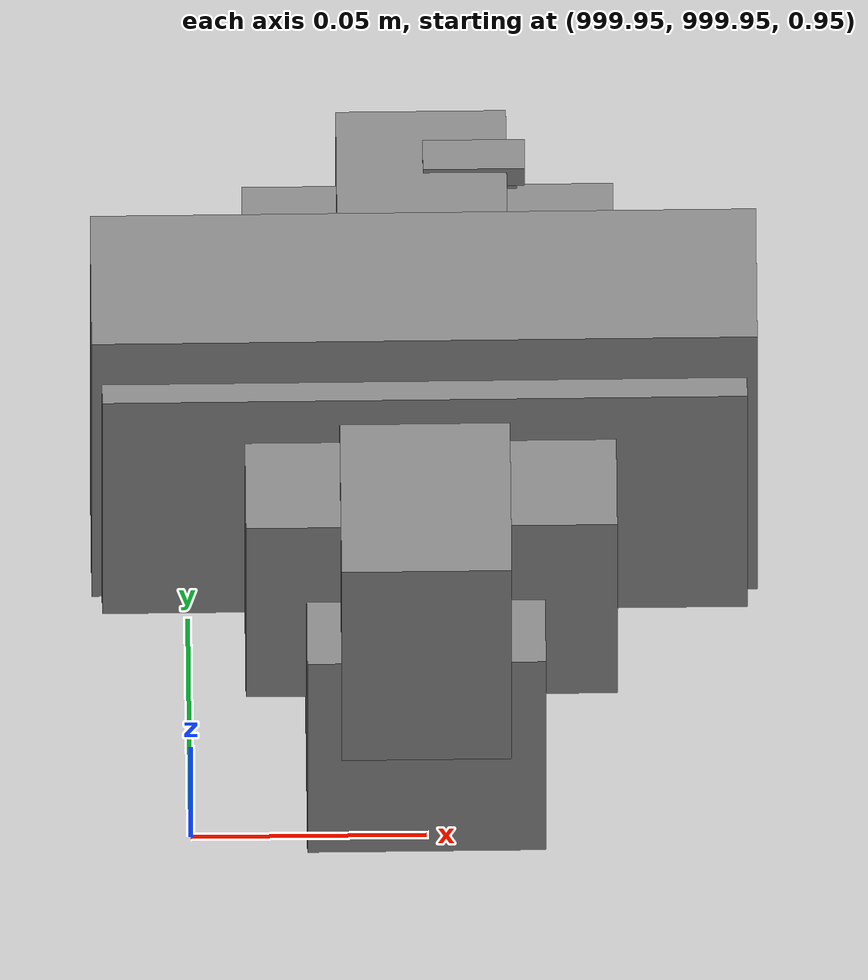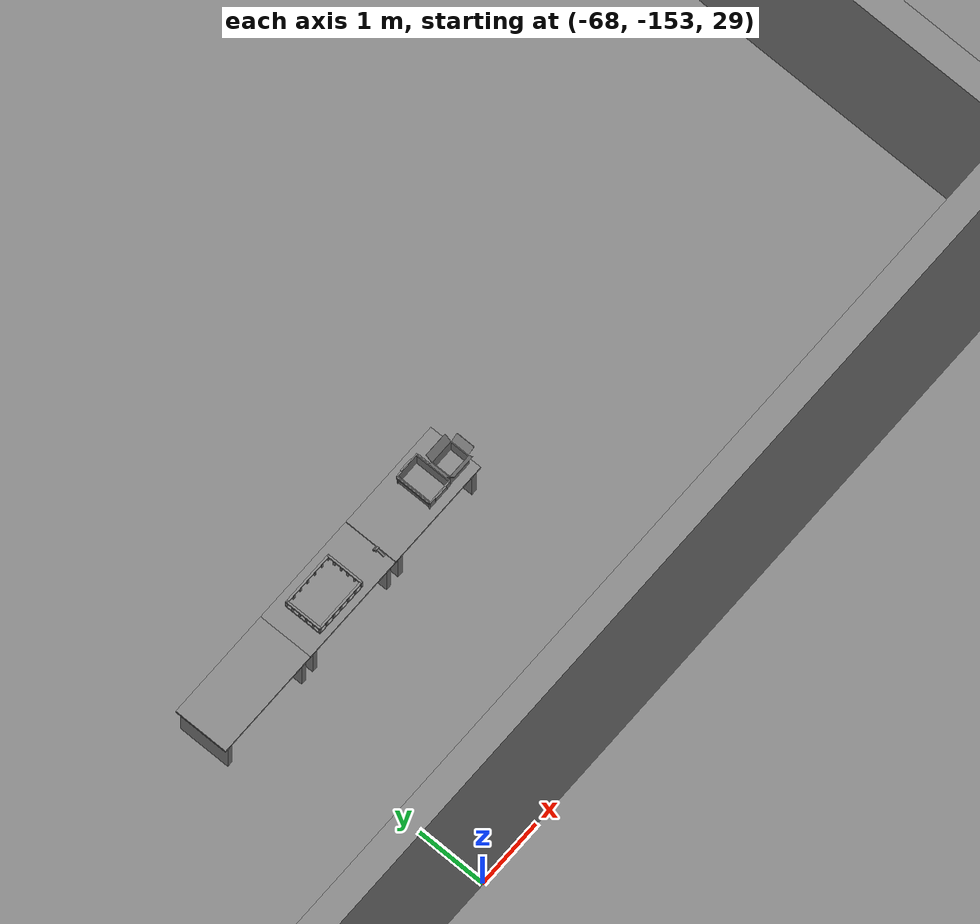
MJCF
<mujoco>
    <option gravity="0.000000000 0.000000000 -9.810000420" timestep="0.0049999999" integrator="implicitfast" density="1.225" viscosity="1.8000001e-05" noslip_iterations="10" iterations="100" sdf_iterations="50">
        <flag multiccd="disable"/>
    </option>
    <size memory="1000M"/>
    <compiler coordinate="local"/>
    <worldbody>
        <light cutoff="30" pos="0 1 1" dir="0 -1 -2"/>
        <light cutoff="30" pos="0 -1 1" dir="0 1 -2"/>
        <body pos="-64.866622925 -149.383972168 30.183746338" euler="89.999984741 89.999946594 0.000000000" name="openloong_gripper_2f85_fix_base_usda_bluebox_01">
            <geom contype="1" conaffinity="1" density="1000" type="box" material="" rgba="0.500000000 0.500000000 0.500000000 1.000000000" solimp="0.899999976 0.949999988 0.001000000" friction="1.000000000 0.005000000 0.000100000" solref="0.020000000 1.000000000" margin="0" condim="3" group="0" pos="0.276580811 0.187225342 0.000068665" quat="0.707106948 0.000077471 0.707106352 0.000077486" size="0.100000001 0.057999998 0.010000000" name="openloong_gripper_2f85_fix_base_usda_geom_CC92336F_2E3A_44B3_A816_C7ADF987C8C0"/>
            <geom contype="1" conaffinity="1" density="1000" type="box" material="" rgba="0.500000000 0.500000000 0.500000000 1.000000000" solimp="0.899999976 0.949999988 0.001000000" friction="1.000000000 0.005000000 0.000100000" solref="0.020000000 1.000000000" margin="0" condim="3" group="0" pos="0.000000000 0.002883911 0.000000000" quat="0.999999881 0.000000000 0.000000000 0.000000000" size="0.254000008 0.003000000 0.172000006" name="openloong_gripper_2f85_fix_base_usda_geom_1647141B_203F_42CB_ADD4_B75C95F6DA18"/>
            <geom contype="1" conaffinity="1" density="1000" type="box" material="" rgba="0.500000000 0.500000000 0.500000000 1.000000000" solimp="0.899999976 0.949999988 0.001000000" friction="1.000000000 0.005000000 0.000100000" solref="0.020000000 1.000000000" margin="0" condim="3" group="0" pos="0.000000000 0.124874115 0.173484802" quat="0.999796331 0.020176515 -0.000000015 0.000000030" size="0.259999990 0.119999997 0.007000000" name="openloong_gripper_2f85_fix_base_usda_geom_BEEE1DA5_8904_48ED_8858_DEF0BCD33CB6"/>
            <geom contype="1" conaffinity="1" density="1000" type="box" material="" rgba="0.500000000 0.500000000 0.500000000 1.000000000" solimp="0.899999976 0.949999988 0.001000000" friction="1.000000000 0.005000000 0.000100000" solref="0.020000000 1.000000000" margin="0" condim="3" group="0" pos="0.000000000 0.124874115 -0.173469543" quat="0.999796331 -0.020176545 -0.000000015 0.000000000" size="0.259999990 0.119999997 0.007000000" name="openloong_gripper_2f85_fix_base_usda_geom_DF5605E8_22A3_4EA5_AA11_A8233CD9E73F"/>
            <geom contype="1" conaffinity="1" density="1000" type="box" material="" rgba="0.500000000 0.500000000 0.500000000 1.000000000" solimp="0.899999976 0.949999988 0.001000000" friction="1.000000000 0.005000000 0.000100000" solref="0.020000000 1.000000000" margin="0" condim="3" group="0" pos="0.000000000 0.214008331 0.188980103" quat="0.999912977 0.013176724 0.000000015 0.000000000" size="0.259999990 0.029999999 0.012500000" name="openloong_gripper_2f85_fix_base_usda_geom_F6807569_518A_4007_90ED_E9C2DB215074"/>
            <geom contype="1" conaffinity="1" density="1000" type="box" material="" rgba="0.500000000 0.500000000 0.500000000 1.000000000" solimp="0.899999976 0.949999988 0.001000000" friction="1.000000000 0.005000000 0.000100000" solref="0.020000000 1.000000000" margin="0" condim="3" group="0" pos="-0.258361816 0.125289917 0.001876831" quat="0.702796936 -0.020792112 0.710783124 0.020769298" size="0.189999998 0.119999997 0.009000000" name="openloong_gripper_2f85_fix_base_usda_geom_310D0AFC_F07C_4C00_95B0_752CD443E4E2"/>
            <geom contype="1" conaffinity="1" density="1000" type="box" material="" rgba="0.500000000 0.500000000 0.500000000 1.000000000" solimp="0.899999976 0.949999988 0.001000000" friction="1.000000000 0.005000000 0.000100000" solref="0.020000000 1.000000000" margin="0" condim="3" group="0" pos="0.000000000 0.214008331 -0.188980103" quat="0.999912977 -0.013176769 0.000000030 0.000000015" size="0.259999990 0.029999999 0.012500000" name="openloong_gripper_2f85_fix_base_usda_geom_674135A5_42E8_461D_B93F_E479ABD9044B"/>
            <geom contype="1" conaffinity="1" density="1000" type="box" material="" rgba="0.500000000 0.500000000 0.500000000 1.000000000" solimp="0.899999976 0.949999988 0.001000000" friction="1.000000000 0.005000000 0.000100000" solref="0.020000000 1.000000000" margin="0" condim="3" group="0" pos="-0.276611328 0.187225342 0.000068665" quat="0.707106650 0.000077441 0.707106709 0.000077456" size="0.100000001 0.057999998 0.010000000" name="openloong_gripper_2f85_fix_base_usda_geom_DF69BE6C_F428_4881_B1A8_D38DB83EF5C3"/>
            <geom contype="1" conaffinity="1" density="1000" type="box" material="" rgba="0.500000000 0.500000000 0.500000000 1.000000000" solimp="0.899999976 0.949999988 0.001000000" friction="1.000000000 0.005000000 0.000100000" solref="0.020000000 1.000000000" margin="0" condim="3" group="0" pos="0.258331299 0.125289917 0.001876831" quat="0.702851415 0.018856421 0.710823774 -0.019329369" size="0.189999998 0.119999997 0.009000000" name="openloong_gripper_2f85_fix_base_usda_geom_D18F35F4_2935_4825_9F07_7CFBCE1B43C0"/>
            <freejoint name="openloong_gripper_2f85_fix_base_usda_bluebox_01_joint"/>
            <site size="0.005000000 0.005000000 0.005000000" rgba="0.500000000 0.500000000 0.500000000 1.000000000" pos="0.000000000 0.000000000 0.000000000" quat="0.999961913 0.008726534 0.000000000 0.000000000" group="0" type="sphere" name="openloong_gripper_2f85_fix_base_usda_bluebox_01site"/>
        </body>
        <body pos="-64.496299744 -149.491867065 30.235729218" euler="0.000000000 0.000000000 89.999946594" name="openloong_gripper_2f85_fix_base_usda_cardboardbox_01">
            <geom contype="1" conaffinity="1" density="1000" type="box" material="" rgba="0.500000000 0.500000000 0.500000000 1.000000000" solimp="0.899999976 0.949999988 0.001000000" friction="1.000000000 0.005000000 0.000100000" solref="0.020000000 1.000000000" margin="0" condim="3" group="0" pos="-0.003166199 -0.004086494 0.005052090" quat="1.000000000 0.000000000 0.000000000 0.000000000" size="0.142499998 0.177500010 0.005000000" name="openloong_gripper_2f85_fix_base_usda_geom_C7D1A2F4_AB15_42DF_8867_F4CA93C07DA5"/>
            <geom contype="1" conaffinity="1" density="1000" type="box" material="" rgba="0.500000000 0.500000000 0.500000000 1.000000000" solimp="0.899999976 0.949999988 0.001000000" friction="1.000000000 0.005000000 0.000100000" solref="0.020000000 1.000000000" margin="0" condim="3" group="0" pos="-0.003166199 0.170316696 0.150570869" quat="1.000000000 0.000000000 0.000000000 0.000000000" size="0.142499998 0.005000000 0.149999991" name="openloong_gripper_2f85_fix_base_usda_geom_260B1C5A_1943_434E_890F_C05183F59817"/>
            <geom contype="1" conaffinity="1" density="1000" type="box" material="" rgba="0.500000000 0.500000000 0.500000000 1.000000000" solimp="0.899999976 0.949999988 0.001000000" friction="1.000000000 0.005000000 0.000100000" solref="0.020000000 1.000000000" margin="0" condim="3" group="0" pos="-0.147399902 -0.005307198 0.150570869" quat="1.000000000 0.000000000 0.000000000 0.000000000" size="0.005000000 0.177500010 0.149999991" name="openloong_gripper_2f85_fix_base_usda_geom_3377D10E_2854_4E1F_8A78_F90B42050463"/>
            <geom contype="1" conaffinity="1" density="1000" type="box" material="" rgba="0.500000000 0.500000000 0.500000000 1.000000000" solimp="0.899999976 0.949999988 0.001000000" friction="1.000000000 0.005000000 0.000100000" solref="0.020000000 1.000000000" margin="0" condim="3" group="0" pos="0.140275955 -0.005307198 0.150570869" quat="1.000000000 0.000000000 0.000000000 0.000000000" size="0.005000000 0.177500010 0.149999991" name="openloong_gripper_2f85_fix_base_usda_geom_9D1A60F5_2603_4C2D_AE50_9585773719F4"/>
            <geom contype="1" conaffinity="1" density="1000" type="box" material="" rgba="0.500000000 0.500000000 0.500000000 1.000000000" solimp="0.899999976 0.949999988 0.001000000" friction="1.000000000 0.005000000 0.000100000" solref="0.020000000 1.000000000" margin="0" condim="3" group="0" pos="-0.003166199 -0.181550980 0.150570869" quat="1.000000000 0.000000000 0.000000000 0.000000000" size="0.142499998 0.005000000 0.149999991" name="openloong_gripper_2f85_fix_base_usda_geom_F6282AC0_6EF3_4AFB_AC9D_4608C8FF0640"/>
            <freejoint name="openloong_gripper_2f85_fix_base_usda_cardboardbox_01_joint"/>
            <site size="0.005000000 0.005000000 0.005000000" rgba="0.500000000 0.500000000 0.500000000 1.000000000" pos="0.000000000 0.000000000 0.000000000" quat="0.999961913 0.008726535 0.000000000 0.000000000" group="0" type="sphere" name="openloong_gripper_2f85_fix_base_usda_site_7D2076C2_8423_41FE_89EF_836C6CC488A9"/>
            <body pos="0.139160156 -0.004048347 0.301930904" euler="-179.999954224 49.383502960 179.999954224" name="openloong_gripper_2f85_fix_base_usda_A1_006">
                <geom contype="1" conaffinity="1" density="1000" type="box" material="" rgba="0.500000000 0.500000000 0.500000000 1.000000000" solimp="0.899999976 0.949999988 0.001000000" friction="1.000000000 0.005000000 0.000100000" solref="0.020000000 1.000000000" margin="0" condim="3" group="0" pos="-0.071587563 0.000009537 0.001745224" quat="0.999999881 0.000000000 0.000000000 0.000000000" size="0.071249999 0.179999992 0.002500000" name="openloong_gripper_2f85_fix_base_usda_geom_6EF96A11_E431_4E39_B799_750467833EF3"/>
                <joint armature="0" stiffness="0.07" damping="0.0099999998" axis="0.000000 1.000000 0.000000" type="hinge" name="openloong_gripper_2f85_fix_base_usda_A1_006"/>
            </body>
            <body pos="-0.145902634 -0.004086494 0.301938057" euler="-180.000000000 -60.000011444 -180.000000000" name="openloong_gripper_2f85_fix_base_usda_A2_006">
                <geom contype="1" conaffinity="1" density="1000" type="box" material="" rgba="0.500000000 0.500000000 0.500000000 1.000000000" solimp="0.899999976 0.949999988 0.001000000" friction="1.000000000 0.005000000 0.000100000" solref="0.020000000 1.000000000" margin="0" condim="3" group="0" pos="0.071268082 0.000009537 0.002717972" quat="0.000002921 0.000000000 -0.000000030 0.999999881" size="0.071249999 0.179999992 0.002500000" name="openloong_gripper_2f85_fix_base_usda_geom_D09D627B_EC7A_4609_A3EE_50194B201694"/>
                <joint armature="0" stiffness="0.07" damping="0.0099999998" axis="0.000000 1.000000 0.000000" type="hinge" name="openloong_gripper_2f85_fix_base_usda_A2_006"/>
            </body>
            <body pos="-0.003385544 0.175991058 0.301930904" euler="-125.858116150 -0.000004561 0.000002331" name="openloong_gripper_2f85_fix_base_usda_B2_006">
                <geom contype="1" conaffinity="1" density="1000" type="box" material="" rgba="0.500000000 0.500000000 0.500000000 1.000000000" solimp="0.899999976 0.949999988 0.001000000" friction="1.000000000 0.005000000 0.000100000" solref="0.020000000 1.000000000" margin="0" condim="3" group="0" pos="0.000009537 -0.070939064 -0.002470016" quat="0.999614120 0.027776197 -0.000000015 0.000000030" size="0.137500003 0.064999998 0.005000000" name="openloong_gripper_2f85_fix_base_usda_geom_36B4F1D4_39FC_4922_82C2_1D618C9FF555"/>
                <joint armature="0" stiffness="0.07" damping="0.0099999998" axis="1.000000 0.000000 0.000000" type="hinge" name="openloong_gripper_2f85_fix_base_usda_B2_006"/>
            </body>
            <body pos="-0.003385544 -0.184140205 0.301938057" euler="147.805557251 0.000000000 0.000000000" name="openloong_gripper_2f85_fix_base_usda_B1_006">
                <geom contype="1" conaffinity="1" density="1000" type="box" material="" rgba="0.500000000 0.500000000 0.500000000 1.000000000" solimp="0.899999976 0.949999988 0.001000000" friction="1.000000000 0.005000000 0.000100000" solref="0.020000000 1.000000000" margin="0" condim="3" group="0" pos="-0.000028610 0.070202351 -0.002703667" quat="0.999614179 -0.027776167 0.000000000 0.000000000" size="0.137500003 0.064999998 0.005000000" name="openloong_gripper_2f85_fix_base_usda_geom_571E85A5_42FB_4B67_9C7A_89E638058F03"/>
                <joint armature="0" stiffness="0.07" damping="0.0099999998" axis="1.000000 0.000000 0.000000" type="hinge" name="openloong_gripper_2f85_fix_base_usda_B1_006"/>
            </body>
        </body>
        <body pos="-65.882858276 -149.481979370 30.229999542" euler="-64.487716675 0.000000000 0.000000000" name="openloong_gripper_2f85_fix_base_usda_Barcode">
            <geom contype="1" conaffinity="1" density="1000" type="box" material="" rgba="0.500000000 0.500000000 0.500000000 1.000000000" solimp="0.899999976 0.949999988 0.001000000" friction="1.000000000 0.005000000 0.000100000" solref="0.020000000 1.000000000" margin="0" condim="3" group="0" pos="0.000000000 0.013038635 0.001419067" quat="0.000000000 0.000000000 0.000000000 1.000000119" size="0.034000002 0.010000000 0.017999999" name="openloong_gripper_2f85_fix_base_usda_geom_C080CC76_9C55_47E0_A29D_1555616D410F"/>
            <geom contype="1" conaffinity="1" density="1000" type="box" material="" rgba="0.500000000 0.500000000 0.500000000 1.000000000" solimp="0.899999976 0.949999988 0.001000000" friction="1.000000000 0.005000000 0.000100000" solref="0.020000000 1.000000000" margin="0" condim="3" group="0" pos="0.000000000 -0.035301208 -0.007095337" quat="0.000000000 0.000000000 -0.043619365 0.999048233" size="0.028999999 0.010000000 0.020000000" name="openloong_gripper_2f85_fix_base_usda_geom_9929BF98_7E90_4D26_9582_8FC2A250A095"/>
            <geom contype="1" conaffinity="1" density="1000" type="box" material="" rgba="0.500000000 0.500000000 0.500000000 1.000000000" solimp="0.899999976 0.949999988 0.001000000" friction="1.000000000 0.005000000 0.000100000" solref="0.020000000 1.000000000" margin="0" condim="3" group="0" pos="0.000000000 -0.043411255 -0.011749268" quat="0.922262907 0.386563420 0.000000000 0.000000000" size="0.026000001 0.010000000 0.020000000" name="openloong_gripper_2f85_fix_base_usda_geom_C659C7DC_80DE_4147_93FB_047EE59B2733"/>
            <geom contype="1" conaffinity="1" density="1000" type="box" material="" rgba="0.500000000 0.500000000 0.500000000 1.000000000" solimp="0.899999976 0.949999988 0.001000000" friction="1.000000000 0.005000000 0.000100000" solref="0.020000000 1.000000000" margin="0" condim="3" group="0" pos="0.000000000 -0.016967773 -0.031860352" quat="0.000000000 0.000000000 0.000000000 1.000000119" size="0.008000000 0.010000000 0.013000000" name="openloong_gripper_2f85_fix_base_usda_geom_C21AE439_2498_406C_9494_EF88395DD3B3"/>
            <geom contype="1" conaffinity="1" density="1000" type="box" material="" rgba="0.500000000 0.500000000 0.500000000 1.000000000" solimp="0.899999976 0.949999988 0.001000000" friction="1.000000000 0.005000000 0.000100000" solref="0.020000000 1.000000000" margin="0" condim="3" group="0" pos="0.000000000 -0.001869202 0.000312805" quat="0.953716993 0.300705761 0.000000000 0.000000000" size="0.032000002 0.010000000 0.018999999" name="openloong_gripper_2f85_fix_base_usda_geom_E6B649F6_8967_4FD5_87AE_6E55045B7A2E"/>
            <geom contype="1" conaffinity="1" density="1000" type="box" material="" rgba="0.500000000 0.500000000 0.500000000 1.000000000" solimp="0.899999976 0.949999988 0.001000000" friction="1.000000000 0.005000000 0.000100000" solref="0.020000000 1.000000000" margin="0" condim="3" group="0" pos="0.000000000 -0.019531250 -0.003173828" quat="0.953716993 0.300705761 0.000000000 0.000000000" size="0.030999999 0.010000000 0.020000000" name="openloong_gripper_2f85_fix_base_usda_geom_E03DEFC2_FA9E_4289_9432_D23C3E94385A"/>
            <geom contype="1" conaffinity="1" density="1000" type="box" material="" rgba="0.500000000 0.500000000 0.500000000 1.000000000" solimp="0.899999976 0.949999988 0.001000000" friction="1.000000000 0.005000000 0.000100000" solref="0.020000000 1.000000000" margin="0" condim="3" group="0" pos="0.000000000 -0.035301208 -0.007095337" quat="0.953716993 0.300705761 0.000000000 0.000000000" size="0.028999999 0.010000000 0.020000000" name="openloong_gripper_2f85_fix_base_usda_geom_D398DA94_02E1_444C_A9CA_B9F7C16D1117"/>
            <geom contype="1" conaffinity="1" density="1000" type="box" material="" rgba="0.500000000 0.500000000 0.500000000 1.000000000" solimp="0.899999976 0.949999988 0.001000000" friction="1.000000000 0.005000000 0.000100000" solref="0.020000000 1.000000000" margin="0" condim="3" group="0" pos="0.000000000 -0.042617798 -0.071121216" quat="0.000000000 0.000000000 0.000000000 1.000000119" size="0.013000000 0.021000000 0.059999999" name="openloong_gripper_2f85_fix_base_usda_geom_A3A71ABA_BB85_4362_A114_60E40DC43964"/>
            <freejoint name="openloong_gripper_2f85_fix_base_usda_Barcode_joint"/>
            <site size="0.005000000 0.005000000 0.005000000" rgba="0.500000000 0.500000000 0.500000000 1.000000000" pos="0.000000000 0.000000000 0.000000000" quat="1.000000000 0.000000000 0.000000000 0.000000000" group="0" type="sphere" name="openloong_gripper_2f85_fix_base_usda_Barcode_site"/>
        </body>
        <body pos="-66.745018005 -149.392349243 30.184000015" euler="0.000000000 0.000000000 89.999946594" name="[22331823718673]_Basket_01">
            <geom contype="1" conaffinity="1" density="1000" type="box" material="" rgba="0.500000000 0.500000000 0.500000000 1.000000000" solimp="0.899999976 0.949999988 0.001000000" friction="1.000000000 0.005000000 0.000100000" solref="0.020000000 1.000000000" margin="0" condim="3" group="0" pos="-0.052425385 0.389207840 0.089787483" quat="0.707107008 0.000000000 0.000000000 0.707106411" size="0.014249999 0.014249999 0.059999999" name="[22331823718673]_geom_D62163EA_1B49_40F4_A2CF_153C2B4A6F13"/>
            <geom contype="1" conaffinity="1" density="1000" type="box" material="" rgba="0.500000000 0.500000000 0.500000000 1.000000000" solimp="0.899999976 0.949999988 0.001000000" friction="1.000000000 0.005000000 0.000100000" solref="0.020000000 1.000000000" margin="0" condim="3" group="0" pos="0.264015198 -0.133043289 0.089787483" quat="0.707107008 0.000000000 0.000000000 0.707106411" size="0.014249999 0.014249999 0.059999999" name="[22331823718673]_geom_D851D0D5_0507_4179_9842_BD3906AD64AB"/>
            <geom contype="1" conaffinity="1" density="1000" type="box" material="" rgba="0.500000000 0.500000000 0.500000000 1.000000000" solimp="0.899999976 0.949999988 0.001000000" friction="1.000000000 0.005000000 0.000100000" solref="0.020000000 1.000000000" margin="0" condim="3" group="0" pos="-0.264015198 -0.265548706 0.089793205" quat="0.707107008 0.000000000 0.000000000 0.707106411" size="0.014249999 0.014249999 0.059999999" name="[22331823718673]_geom_304A253B_8AB6_4A68_8841_1799E386B1B2"/>
            <geom contype="1" conaffinity="1" density="1000" type="box" material="" rgba="0.500000000 0.500000000 0.500000000 1.000000000" solimp="0.899999976 0.949999988 0.001000000" friction="1.000000000 0.005000000 0.000100000" solref="0.020000000 1.000000000" margin="0" condim="3" group="0" pos="-0.160263062 -0.389322281 0.089793205" quat="0.707107008 0.000000000 0.000000000 0.707106411" size="0.014249999 0.014249999 0.059999999" name="[22331823718673]_geom_31A616EF_472B_4C0C_83AD_D34F99E7950C"/>
            <geom contype="1" conaffinity="1" density="1000" type="box" material="" rgba="0.500000000 0.500000000 0.500000000 1.000000000" solimp="0.899999976 0.949999988 0.001000000" friction="1.000000000 0.005000000 0.000100000" solref="0.020000000 1.000000000" margin="0" condim="3" group="0" pos="0.162265778 -0.389322281 0.089787483" quat="0.707107008 0.000000000 0.000000000 0.707106411" size="0.014249999 0.014249999 0.059999999" name="[22331823718673]_geom_61A1C50F_253A_4ECA_A3E3_7E391417B671"/>
            <geom contype="1" conaffinity="1" density="1000" type="box" material="" rgba="0.500000000 0.500000000 0.500000000 1.000000000" solimp="0.899999976 0.949999988 0.001000000" friction="1.000000000 0.005000000 0.000100000" solref="0.020000000 1.000000000" margin="0" condim="3" group="0" pos="0.264015198 0.389207840 0.089787483" quat="0.707107008 0.000000000 0.000000000 0.707106411" size="0.014249999 0.014249999 0.059999999" name="[22331823718673]_geom_EB66CDB2_CB3E_45CE_99AE_1FD00B48E297"/>
            <geom contype="1" conaffinity="1" density="1000" type="box" material="" rgba="0.500000000 0.500000000 0.500000000 1.000000000" solimp="0.899999976 0.949999988 0.001000000" friction="1.000000000 0.005000000 0.000100000" solref="0.020000000 1.000000000" margin="0" condim="3" group="0" pos="-0.264015198 -0.133043289 0.089793205" quat="0.707107008 0.000000000 0.000000000 0.707106411" size="0.014249999 0.014249999 0.059999999" name="[22331823718673]_geom_29367ACC_BA06_4254_BF6D_29E7ADE14C23"/>
            <geom contype="1" conaffinity="1" density="1000" type="box" material="" rgba="0.500000000 0.500000000 0.500000000 1.000000000" solimp="0.899999976 0.949999988 0.001000000" friction="1.000000000 0.005000000 0.000100000" solref="0.020000000 1.000000000" margin="0" condim="3" group="0" pos="-0.264026642 0.269256592 0.089793205" quat="0.707107008 0.000000000 0.000000000 0.707106411" size="0.014249999 0.014249999 0.059999999" name="[22331823718673]_geom_1E0A7D03_CB07_4D8C_AC4E_D5415A9F3313"/>
            <geom contype="1" conaffinity="1" density="1000" type="box" material="" rgba="0.500000000 0.500000000 0.500000000 1.000000000" solimp="0.899999976 0.949999988 0.001000000" friction="1.000000000 0.005000000 0.000100000" solref="0.020000000 1.000000000" margin="0" condim="3" group="0" pos="0.054462433 0.389207840 0.089787483" quat="0.707107008 0.000000000 0.000000000 0.707106411" size="0.014249999 0.014249999 0.059999999" name="[22331823718673]_geom_A9FC210F_A2AC_444E_8863_7144F382168A"/>
            <geom contype="1" conaffinity="1" density="1000" type="box" material="" rgba="0.500000000 0.500000000 0.500000000 1.000000000" solimp="0.899999976 0.949999988 0.001000000" friction="1.000000000 0.005000000 0.000100000" solref="0.020000000 1.000000000" margin="0" condim="3" group="0" pos="0.054462433 -0.389322281 0.089787483" quat="0.707107008 0.000000000 0.000000000 0.707106411" size="0.014249999 0.014249999 0.059999999" name="[22331823718673]_geom_C0791A2C_5004_4A52_894D_CE811DB9267E"/>
            <geom contype="1" conaffinity="1" density="1000" type="box" material="" rgba="0.500000000 0.500000000 0.500000000 1.000000000" solimp="0.899999976 0.949999988 0.001000000" friction="1.000000000 0.005000000 0.000100000" solref="0.020000000 1.000000000" margin="0" condim="3" group="0" pos="0.264015198 0.269256592 0.089793205" quat="0.707107008 0.000000000 0.000000000 0.707106411" size="0.014249999 0.014249999 0.059999999" name="[22331823718673]_geom_590B3E7D_35A9_4B61_9F62_121FA9189442"/>
            <geom contype="1" conaffinity="1" density="1000" type="box" material="" rgba="0.500000000 0.500000000 0.500000000 1.000000000" solimp="0.899999976 0.949999988 0.001000000" friction="1.000000000 0.005000000 0.000100000" solref="0.020000000 1.000000000" margin="0" condim="3" group="0" pos="0.264015198 -0.389322281 0.089787483" quat="0.707107008 0.000000000 0.000000000 0.707106411" size="0.014249999 0.014249999 0.059999999" name="[22331823718673]_geom_A3E6BA14_FE80_46FA_99F5_3797935D5040"/>
            <geom contype="1" conaffinity="1" density="1000" type="box" material="" rgba="0.500000000 0.500000000 0.500000000 1.000000000" solimp="0.899999976 0.949999988 0.001000000" friction="1.000000000 0.005000000 0.000100000" solref="0.020000000 1.000000000" margin="0" condim="3" group="0" pos="0.000000000 0.000000000 0.015998840" quat="0.707107008 0.000000000 0.000000000 0.707106411" size="0.403499991 0.279000014 0.015750000" name="[22331823718673]_geom_45BFB3E5_0E34_4461_9199_11CA79ADF0B3"/>
            <geom contype="1" conaffinity="1" density="1000" type="box" material="" rgba="0.500000000 0.500000000 0.500000000 1.000000000" solimp="0.899999976 0.949999988 0.001000000" friction="1.000000000 0.005000000 0.000100000" solref="0.020000000 1.000000000" margin="0" condim="3" group="0" pos="0.000000000 -0.389476776 0.163619041" quat="0.707107008 0.000000000 0.000000000 0.707106411" size="0.015000000 0.277500004 0.015750000" name="[22331823718673]_geom_91882B23_A819_406C_8BDD_4D2B81E1572B"/>
            <geom contype="1" conaffinity="1" density="1000" type="box" material="" rgba="0.500000000 0.500000000 0.500000000 1.000000000" solimp="0.899999976 0.949999988 0.001000000" friction="1.000000000 0.005000000 0.000100000" solref="0.020000000 1.000000000" margin="0" condim="3" group="0" pos="0.162265778 0.389207840 0.089787483" quat="0.707107008 0.000000000 0.000000000 0.707106411" size="0.014249999 0.014249999 0.059999999" name="[22331823718673]_geom_9BB855F6_2A47_41D9_9398_DCEF41C225D8"/>
            <geom contype="1" conaffinity="1" density="1000" type="box" material="" rgba="0.500000000 0.500000000 0.500000000 1.000000000" solimp="0.899999976 0.949999988 0.001000000" friction="1.000000000 0.005000000 0.000100000" solref="0.020000000 1.000000000" margin="0" condim="3" group="0" pos="0.000000000 0.389471054 0.163619041" quat="0.707107008 0.000000000 0.000000000 0.707106411" size="0.015000000 0.277500004 0.015750000" name="[22331823718673]_geom_9D51B0C3_30F9_4532_A2BF_14B6B80090CF"/>
            <geom contype="1" conaffinity="1" density="1000" type="box" material="" rgba="0.500000000 0.500000000 0.500000000 1.000000000" solimp="0.899999976 0.949999988 0.001000000" friction="1.000000000 0.005000000 0.000100000" solref="0.020000000 1.000000000" margin="0" condim="3" group="0" pos="-0.263511658 0.000000000 0.163619041" quat="0.707107008 0.000000000 0.000000000 0.707106411" size="0.403499991 0.015000000 0.015750000" name="[22331823718673]_geom_D2CB02CF_9953_43EA_B7E0_63D48BF63A50"/>
            <geom contype="1" conaffinity="1" density="1000" type="box" material="" rgba="0.500000000 0.500000000 0.500000000 1.000000000" solimp="0.899999976 0.949999988 0.001000000" friction="1.000000000 0.005000000 0.000100000" solref="0.020000000 1.000000000" margin="0" condim="3" group="0" pos="-0.264015198 0.141334534 0.089793205" quat="0.707107008 0.000000000 0.000000000 0.707106411" size="0.014249999 0.014249999 0.059999999" name="[22331823718673]_geom_AB9F3A3C_F5D0_46A6_A2B8_75E94B6160E9"/>
            <geom contype="1" conaffinity="1" density="1000" type="box" material="" rgba="0.500000000 0.500000000 0.500000000 1.000000000" solimp="0.899999976 0.949999988 0.001000000" friction="1.000000000 0.005000000 0.000100000" solref="0.020000000 1.000000000" margin="0" condim="3" group="0" pos="0.264015198 -0.265548706 0.089787483" quat="0.707107008 0.000000000 0.000000000 0.707106411" size="0.014249999 0.014249999 0.059999999" name="[22331823718673]_geom_CCBAD9A6_624B_4C04_848F_5076D1A5E5D4"/>
            <geom contype="1" conaffinity="1" density="1000" type="box" material="" rgba="0.500000000 0.500000000 0.500000000 1.000000000" solimp="0.899999976 0.949999988 0.001000000" friction="1.000000000 0.005000000 0.000100000" solref="0.020000000 1.000000000" margin="0" condim="3" group="0" pos="-0.160263062 0.389207840 0.089787483" quat="0.707107008 0.000000000 0.000000000 0.707106411" size="0.014249999 0.014249999 0.059999999" name="[22331823718673]_geom_4B675A48_D0B4_4CCC_9340_94DD74BCC063"/>
            <geom contype="1" conaffinity="1" density="1000" type="box" material="" rgba="0.500000000 0.500000000 0.500000000 1.000000000" solimp="0.899999976 0.949999988 0.001000000" friction="1.000000000 0.005000000 0.000100000" solref="0.020000000 1.000000000" margin="0" condim="3" group="0" pos="-0.052425385 -0.389322281 0.089787483" quat="0.707107008 0.000000000 0.000000000 0.707106411" size="0.014249999 0.014249999 0.059999999" name="[22331823718673]_geom_1642F45D_37FF_4244_B944_62148AF15438"/>
            <geom contype="1" conaffinity="1" density="1000" type="box" material="" rgba="0.500000000 0.500000000 0.500000000 1.000000000" solimp="0.899999976 0.949999988 0.001000000" friction="1.000000000 0.005000000 0.000100000" solref="0.020000000 1.000000000" margin="0" condim="3" group="0" pos="-0.264026642 -0.389322281 0.089793205" quat="0.707107008 0.000000000 0.000000000 0.707106411" size="0.014249999 0.014249999 0.059999999" name="[22331823718673]_geom_2381C827_690B_41E4_A40F_CCEE186607D1"/>
            <geom contype="1" conaffinity="1" density="1000" type="box" material="" rgba="0.500000000 0.500000000 0.500000000 1.000000000" solimp="0.899999976 0.949999988 0.001000000" friction="1.000000000 0.005000000 0.000100000" solref="0.020000000 1.000000000" margin="0" condim="3" group="0" pos="0.264015198 0.141334534 0.089787483" quat="0.707107008 0.000000000 0.000000000 0.707106411" size="0.014249999 0.014249999 0.059999999" name="[22331823718673]_geom_FA559CC1_F373_447D_9627_5EC4E63A6A62"/>
            <geom contype="1" conaffinity="1" density="1000" type="box" material="" rgba="0.500000000 0.500000000 0.500000000 1.000000000" solimp="0.899999976 0.949999988 0.001000000" friction="1.000000000 0.005000000 0.000100000" solref="0.020000000 1.000000000" margin="0" condim="3" group="0" pos="-0.264015198 0.389207840 0.089793205" quat="0.707107008 0.000000000 0.000000000 0.707106411" size="0.014249999 0.014249999 0.059999999" name="[22331823718673]_geom_540E1966_D063_4947_A6F6_9B369DD44803"/>
            <geom contype="1" conaffinity="1" density="1000" type="box" material="" rgba="0.500000000 0.500000000 0.500000000 1.000000000" solimp="0.899999976 0.949999988 0.001000000" friction="1.000000000 0.005000000 0.000100000" solref="0.020000000 1.000000000" margin="0" condim="3" group="0" pos="0.264015198 0.004480362 0.089787483" quat="0.707107008 0.000000000 0.000000000 0.707106411" size="0.014249999 0.014249999 0.059999999" name="[22331823718673]_geom_B5B0C545_6EEC_41B7_BCB7_F37D33719D61"/>
            <geom contype="1" conaffinity="1" density="1000" type="box" material="" rgba="0.500000000 0.500000000 0.500000000 1.000000000" solimp="0.899999976 0.949999988 0.001000000" friction="1.000000000 0.005000000 0.000100000" solref="0.020000000 1.000000000" margin="0" condim="3" group="0" pos="0.263694763 -0.000011444 0.163619041" quat="0.707107008 0.000000000 0.000000000 0.707106411" size="0.403499991 0.015000000 0.015750000" name="[22331823718673]_geom_6222921A_E994_4165_B460_9AD55FC1A3A1"/>
            <geom contype="1" conaffinity="1" density="1000" type="box" material="" rgba="0.500000000 0.500000000 0.500000000 1.000000000" solimp="0.899999976 0.949999988 0.001000000" friction="1.000000000 0.005000000 0.000100000" solref="0.020000000 1.000000000" margin="0" condim="3" group="0" pos="-0.264015198 0.004480362 0.089793205" quat="0.707107008 0.000000000 0.000000000 0.707106411" size="0.014249999 0.014249999 0.059999999" name="[22331823718673]_geom_70ACAFE6_B60B_4165_BE9F_FBF4B545C56C"/>
            <freejoint name="[22331823718673]_joint_712A6B97_3B8A_4557_9ADA_67C07FF86470"/>
        </body>
        <body pos="0.000000000 0.000000000 0.000000000" euler="0.000000000 0.000000000 0.000000000" name="Static Objects_Static Objects">
            <geom contype="1" conaffinity="1" density="1000" type="box" material="" rgba="0.500000000 0.500000000 0.500000000 1.000000000" solimp="0.899999976 0.949999988 0.001000000" friction="1.000000000 0.005000000 0.000100000" solref="0.020000000 1.000000000" margin="0" condim="3" group="0" pos="-67.544113159 -149.365814209 29.727830887" quat="0.500000417 0.499999970 0.499999553 0.499999970" size="0.381000012 0.319999993 0.041000001" name="Static Objects_geom_57838BCD_3CA1_4203_8C30_1E49B835AB24"/>
            <geom contype="1" conaffinity="1" density="1000" type="box" material="" rgba="0.500000000 0.500000000 0.500000000 1.000000000" solimp="0.899999976 0.949999988 0.001000000" friction="1.000000000 0.005000000 0.000100000" solref="0.020000000 1.000000000" margin="0" condim="3" group="0" pos="-68.239501953 -149.365814209 30.086868286" quat="0.500000417 0.499999970 0.499999553 0.499999970" size="0.370999992 0.039500002 0.745000005" name="Static Objects_geom_5BF28626_B389_4758_B0E8_97D2444D6097"/>
            <geom contype="1" conaffinity="1" density="1000" type="box" material="" rgba="0.500000000 0.500000000 0.500000000 1.000000000" solimp="0.899999976 0.949999988 0.001000000" friction="1.000000000 0.005000000 0.000100000" solref="0.020000000 1.000000000" margin="0" condim="3" group="0" pos="-68.239501953 -149.365814209 30.147235870" quat="0.500000417 0.499999970 0.499999553 0.499999970" size="0.400000006 0.022000000 0.800000012" name="Static Objects_geom_1FFE3C1A_063A_49C5_AA74_44A3E29C4286"/>
            <geom contype="1" conaffinity="1" density="1000" type="box" material="" rgba="0.500000000 0.500000000 0.500000000 1.000000000" solimp="0.899999976 0.949999988 0.001000000" friction="1.000000000 0.005000000 0.000100000" solref="0.020000000 1.000000000" margin="0" condim="3" group="0" pos="-68.934890747 -149.365814209 29.727830887" quat="0.500000417 0.499999970 0.499999553 0.499999970" size="0.381000012 0.319999993 0.041000001" name="Static Objects_geom_1C4B20D9_F7B0_4373_AF38_F6473BBA5ADF"/>
            <geom contype="1" conaffinity="1" density="1000" type="box" material="" rgba="0.500000000 0.500000000 0.500000000 1.000000000" solimp="0.899999976 0.949999988 0.001000000" friction="1.000000000 0.005000000 0.000100000" solref="0.020000000 1.000000000" margin="0" condim="3" group="0" pos="-68.239501953 -149.365814209 29.561563492" quat="0.500000417 0.499999970 0.499999553 0.499999970" size="0.020000000 0.022000000 0.660000026" name="Static Objects_geom_A328115C_A6D7_4B14_8E46_FCF56F995C8C"/>
            <geom contype="1" conaffinity="1" density="1000" type="box" material="" rgba="0.500000000 0.500000000 0.500000000 1.000000000" solimp="0.899999976 0.949999988 0.001000000" friction="1.000000000 0.005000000 0.000100000" solref="0.020000000 1.000000000" margin="0" condim="3" group="0" pos="-65.945671082 -149.365814209 29.727830887" quat="0.500000417 0.499999970 0.499999553 0.499999970" size="0.381000012 0.319999993 0.041000001" name="Static Objects_geom_2D8247CA_20F7_45C4_9FD3_983AC43C113D"/>
            <geom contype="1" conaffinity="1" density="1000" type="box" material="" rgba="0.500000000 0.500000000 0.500000000 1.000000000" solimp="0.899999976 0.949999988 0.001000000" friction="1.000000000 0.005000000 0.000100000" solref="0.020000000 1.000000000" margin="0" condim="3" group="0" pos="-66.641059875 -149.365814209 30.086868286" quat="0.500000417 0.499999970 0.499999553 0.499999970" size="0.370999992 0.039500002 0.745000005" name="Static Objects_geom_E782BBDD_8587_41D9_85C0_ADC6DD1D3B55"/>
            <geom contype="1" conaffinity="1" density="1000" type="box" material="" rgba="0.500000000 0.500000000 0.500000000 1.000000000" solimp="0.899999976 0.949999988 0.001000000" friction="1.000000000 0.005000000 0.000100000" solref="0.020000000 1.000000000" margin="0" condim="3" group="0" pos="-66.641059875 -149.365814209 30.147235870" quat="0.500000417 0.499999970 0.499999553 0.499999970" size="0.400000006 0.022000000 0.800000012" name="Static Objects_geom_06FB733A_7443_448D_A06A_E2B4FD9F1110"/>
            <geom contype="1" conaffinity="1" density="1000" type="box" material="" rgba="0.500000000 0.500000000 0.500000000 1.000000000" solimp="0.899999976 0.949999988 0.001000000" friction="1.000000000 0.005000000 0.000100000" solref="0.020000000 1.000000000" margin="0" condim="3" group="0" pos="-67.336448669 -149.365814209 29.727830887" quat="0.500000417 0.499999970 0.499999553 0.499999970" size="0.381000012 0.319999993 0.041000001" name="Static Objects_geom_A1D23503_8BFE_4461_96B7_C3CD717D2D8F"/>
            <geom contype="1" conaffinity="1" density="1000" type="box" material="" rgba="0.500000000 0.500000000 0.500000000 1.000000000" solimp="0.899999976 0.949999988 0.001000000" friction="1.000000000 0.005000000 0.000100000" solref="0.020000000 1.000000000" margin="0" condim="3" group="0" pos="-66.641059875 -149.365814209 29.561563492" quat="0.500000417 0.499999970 0.499999553 0.499999970" size="0.020000000 0.022000000 0.660000026" name="Static Objects_geom_EE82C5C4_BA7F_4FFE_8E21_5186BDD6F0AA"/>
            <geom contype="1" conaffinity="1" density="1000" type="box" material="" rgba="0.500000000 0.500000000 0.500000000 1.000000000" solimp="0.899999976 0.949999988 0.001000000" friction="1.000000000 0.005000000 0.000100000" solref="0.020000000 1.000000000" margin="0" condim="3" group="0" pos="-64.338577271 -149.365814209 29.727830887" quat="0.500000417 0.499999970 0.499999553 0.499999970" size="0.381000012 0.319999993 0.041000001" name="Static Objects_geom_4B04B619_1DA3_4F8C_BD78_5E801A6BF643"/>
            <geom contype="1" conaffinity="1" density="1000" type="box" material="" rgba="0.500000000 0.500000000 0.500000000 1.000000000" solimp="0.899999976 0.949999988 0.001000000" friction="1.000000000 0.005000000 0.000100000" solref="0.020000000 1.000000000" margin="0" condim="3" group="0" pos="-65.033966064 -149.365814209 30.086868286" quat="0.500000417 0.499999970 0.499999553 0.499999970" size="0.370999992 0.039500002 0.745000005" name="Static Objects_geom_4ECFE9FA_D91F_4C8B_BACE_1F5FE07BC0D0"/>
            <geom contype="1" conaffinity="1" density="1000" type="box" material="" rgba="0.500000000 0.500000000 0.500000000 1.000000000" solimp="0.899999976 0.949999988 0.001000000" friction="1.000000000 0.005000000 0.000100000" solref="0.020000000 1.000000000" margin="0" condim="3" group="0" pos="-65.033966064 -149.365814209 30.147235870" quat="0.500000417 0.499999970 0.499999553 0.499999970" size="0.400000006 0.022000000 0.800000012" name="Static Objects_geom_B8B0D971_8B9A_4B5A_A8BD_959320380AE3"/>
            <geom contype="1" conaffinity="1" density="1000" type="box" material="" rgba="0.500000000 0.500000000 0.500000000 1.000000000" solimp="0.899999976 0.949999988 0.001000000" friction="1.000000000 0.005000000 0.000100000" solref="0.020000000 1.000000000" margin="0" condim="3" group="0" pos="-65.729354858 -149.365814209 29.727830887" quat="0.500000417 0.499999970 0.499999553 0.499999970" size="0.381000012 0.319999993 0.041000001" name="Static Objects_geom_C02B9C09_875C_4472_B00E_A5019FBA41AE"/>
            <geom contype="1" conaffinity="1" density="1000" type="box" material="" rgba="0.500000000 0.500000000 0.500000000 1.000000000" solimp="0.899999976 0.949999988 0.001000000" friction="1.000000000 0.005000000 0.000100000" solref="0.020000000 1.000000000" margin="0" condim="3" group="0" pos="-65.033966064 -149.365814209 29.561563492" quat="0.500000417 0.499999970 0.499999553 0.499999970" size="0.020000000 0.022000000 0.660000026" name="Static Objects_geom_40112FF7_7787_4B10_877B_9561B644BDCE"/>
            <geom contype="1" conaffinity="1" density="1000" type="box" material="" rgba="0.500000000 0.500000000 0.500000000 1.000000000" solimp="0.899999976 0.949999988 0.001000000" friction="1.000000000 0.005000000 0.000100000" solref="0.020000000 1.000000000" margin="0" condim="3" group="0" pos="-61.754566193 -137.853729248 33.906845093" quat="0.707107067 0.000000000 0.000000000 0.707106471" size="0.759999990 0.759999990 4.500000000" name="Static Objects_geom_9D817895_315E_483B_A64E_A92318B90AEE"/>
            <geom contype="1" conaffinity="1" density="1000" type="box" material="" rgba="0.500000000 0.500000000 0.500000000 1.000000000" solimp="0.899999976 0.949999988 0.001000000" friction="1.000000000 0.005000000 0.000100000" solref="0.020000000 1.000000000" margin="0" condim="3" group="0" pos="-57.511135101 -144.927108765 31.707921982" quat="1.000000000 0.000000000 0.000000000 0.000000000" size="0.200000003 8.000000000 2.299999952" name="Static Objects_geom_11DC838F_4FD2_404D_8213_F96D6026E435"/>
            <geom contype="1" conaffinity="1" density="1000" type="box" material="" rgba="0.500000000 0.500000000 0.500000000 1.000000000" solimp="0.899999976 0.949999988 0.001000000" friction="1.000000000 0.005000000 0.000100000" solref="0.020000000 1.000000000" margin="0" condim="3" group="0" pos="-80.517646790 -157.574050903 31.688196182" quat="0.707107067 0.000000000 0.000000000 0.707106471" size="0.600000024 0.600000024 2.299999952" name="Static Objects_geom_71562A95_294D_4D5C_BCC0_7EA7B911DE75"/>
            <geom contype="1" conaffinity="1" density="1000" type="box" material="" rgba="0.500000000 0.500000000 0.500000000 1.000000000" solimp="0.899999976 0.949999988 0.001000000" friction="1.000000000 0.005000000 0.000100000" solref="0.020000000 1.000000000" margin="0" condim="3" group="0" pos="-80.711044312 -147.414932251 31.666158676" quat="1.000000000 0.000000000 0.000000000 0.000000000" size="0.200000003 10.000000000 2.299999952" name="Static Objects_geom_DEB0E37C_40B2_4471_A0C3_3D740B203E8D"/>
            <geom contype="1" conaffinity="1" density="1000" type="box" material="" rgba="0.500000000 0.500000000 0.500000000 1.000000000" solimp="0.899999976 0.949999988 0.001000000" friction="1.000000000 0.005000000 0.000100000" solref="0.020000000 1.000000000" margin="0" condim="3" group="0" pos="-57.687217712 -137.434692383 31.688196182" quat="0.707107067 0.000000000 0.000000000 0.707106471" size="0.600000024 0.600000024 2.299999952" name="Static Objects_geom_5C41987E_C443_40C4_B051_FE4DDA110450"/>
            <geom contype="1" conaffinity="1" density="1000" type="box" material="" rgba="0.500000000 0.500000000 0.500000000 1.000000000" solimp="0.899999976 0.949999988 0.001000000" friction="1.000000000 0.005000000 0.000100000" solref="0.020000000 1.000000000" margin="0" condim="3" group="0" pos="-69.537033081 -140.263229370 31.714921951" quat="0.707107067 0.000000000 0.000000000 0.707106471" size="0.759999990 4.500000000 2.299999952" name="Static Objects_geom_ED3AE12C_553D_4309_A162_C3A401CEDB8C"/>
            <geom contype="1" conaffinity="1" density="1000" type="box" material="" rgba="0.500000000 0.500000000 0.500000000 1.000000000" solimp="0.899999976 0.949999988 0.001000000" friction="1.000000000 0.005000000 0.000100000" solref="0.020000000 1.000000000" margin="0" condim="3" group="0" pos="-80.073638916 -137.853713989 33.906845093" quat="0.707107067 0.000000000 0.000000000 0.707106471" size="0.759999990 0.759999990 4.500000000" name="Static Objects_geom_85779E01_4367_4512_A11E_4CC0E3B731B6"/>
            <geom contype="1" conaffinity="1" density="1000" type="box" material="" rgba="0.500000000 0.500000000 0.500000000 1.000000000" solimp="0.899999976 0.949999988 0.001000000" friction="1.000000000 0.005000000 0.000100000" solref="0.020000000 1.000000000" margin="0" condim="3" group="0" pos="-73.406707764 -155.734664917 31.707921982" quat="1.000000000 0.000000000 0.000000000 0.000000000" size="0.200000003 3.000000000 2.299999952" name="Static Objects_geom_0F430C58_997E_4200_B405_2B96A98E6CC8"/>
            <geom contype="1" conaffinity="1" density="1000" type="box" material="" rgba="0.500000000 0.500000000 0.500000000 1.000000000" solimp="0.899999976 0.949999988 0.001000000" friction="1.000000000 0.005000000 0.000100000" solref="0.020000000 1.000000000" margin="0" condim="3" group="0" pos="-68.497543335 -137.448257446 31.707921982" quat="0.707107067 0.000000000 0.000000000 0.707106471" size="0.200000003 14.000000000 2.299999952" name="Static Objects_geom_79E21799_631E_4053_83CC_AEB36AB8A777"/>
            <geom contype="1" conaffinity="1" density="1000" type="cylinder" material="" rgba="0.500000000 0.500000000 0.500000000 1.000000000" solimp="0.899999976 0.949999988 0.001000000" friction="1.000000000 0.005000000 0.000100000" solref="0.020000000 1.000000000" margin="0" condim="3" group="0" pos="-68.868522644 -142.134506226 31.711090088" quat="0.707107067 0.000000000 0.000000000 0.707106471" size="0.509999990 2.299999952 1.000000000" name="Static Objects_geom_A4CD13AB_F66E_49A0_B546_A1871CDE8FF9"/>
            <geom contype="1" conaffinity="1" density="1000" type="plane" material="" rgba="0.500000000 0.500000000 0.500000000 1.000000000" solimp="0.899999976 0.949999988 0.001000000" friction="1.000000000 0.005000000 0.000100000" solref="0.020000000 1.000000000" margin="0" condim="3" group="0" pos="-72.873703003 -147.131927490 29.409669876" quat="1.000000000 0.000000000 0.000000000 0.000000000" size="18.000000000 14.000000000 1.000000000" name="Static Objects_geom_389F5DB8_E1F6_4610_9C20_43C52F387C0C"/>
            <geom contype="1" conaffinity="1" density="1000" type="box" material="" rgba="0.500000000 0.500000000 0.500000000 1.000000000" solimp="0.899999976 0.949999988 0.001000000" friction="1.000000000 0.005000000 0.000100000" solref="0.020000000 1.000000000" margin="0" condim="3" group="0" pos="-79.943580627 -157.782272339 31.707921982" quat="0.707107067 0.000000000 0.000000000 0.707106471" size="0.200000003 7.000000000 2.299999952" name="Static Objects_geom_0EE3142B_2206_4798_9496_B31192EE2AE5"/>
            <geom contype="1" conaffinity="1" density="1000" type="box" material="" rgba="0.500000000 0.500000000 0.500000000 1.000000000" solimp="0.899999976 0.949999988 0.001000000" friction="1.000000000 0.005000000 0.000100000" solref="0.020000000 1.000000000" margin="0" condim="3" group="0" pos="-65.421028137 -152.903442383 31.707921982" quat="0.707107067 0.000000000 0.000000000 0.707106471" size="0.200000003 7.800000191 2.299999952" name="Static Objects_geom_53B962A1_879C_43B9_8E26_0BE043280972"/>
            <geom contype="1" conaffinity="1" density="1000" type="box" material="" rgba="0.500000000 0.500000000 0.500000000 1.000000000" solimp="0.899999976 0.949999988 0.001000000" friction="1.000000000 0.005000000 0.000100000" solref="0.020000000 1.000000000" margin="0" condim="3" group="0" pos="-74.776908875 -149.964416504 31.688196182" quat="1.000000000 0.000000000 0.000000000 0.000000000" size="0.600000024 0.409999996 2.299999952" name="Static Objects_geom_B4986E69_F37E_4547_9231_C6F2C0CDBF50"/>
            <geom contype="1" conaffinity="1" density="1000" type="cylinder" material="" rgba="0.500000000 0.500000000 0.500000000 1.000000000" solimp="0.899999976 0.949999988 0.001000000" friction="1.000000000 0.005000000 0.000100000" solref="0.020000000 1.000000000" margin="0" condim="3" group="0" pos="-60.161884308 -142.134506226 31.711090088" quat="0.707107067 0.000000000 0.000000000 0.707106471" size="0.509999990 2.299999952 1.000000000" name="Static Objects_geom_0D6F1180_1A3A_411F_B608_5C9FF9A29CC8"/>
            <geom contype="1" conaffinity="1" density="1000" type="cylinder" material="" rgba="0.500000000 0.500000000 0.500000000 1.000000000" solimp="0.899999976 0.949999988 0.001000000" friction="1.000000000 0.005000000 0.000100000" solref="0.020000000 1.000000000" margin="0" condim="3" group="0" pos="-75.382453918 -149.963455200 31.711090088" quat="0.707107067 0.000000000 0.000000000 0.707106471" size="0.409999996 2.299999952 1.000000000" name="Static Objects_geom_CA5705E7_D42C_4F07_B79E_5F02586773F5"/>
            <geom contype="1" conaffinity="1" density="1000" type="cylinder" material="" rgba="0.500000000 0.500000000 0.500000000 1.000000000" solimp="0.899999976 0.949999988 0.001000000" friction="1.000000000 0.005000000 0.000100000" solref="0.020000000 1.000000000" margin="0" condim="3" group="0" pos="-74.154960632 -149.963455200 31.711090088" quat="0.707107067 0.000000000 0.000000000 0.707106471" size="0.409999996 2.299999952 1.000000000" name="Static Objects_geom_E0525CA8_C426_4250_B4A4_77F754C2803D"/>
            <geom contype="1" conaffinity="1" density="1000" type="cylinder" material="" rgba="0.500000000 0.500000000 0.500000000 1.000000000" solimp="0.899999976 0.949999988 0.001000000" friction="1.000000000 0.005000000 0.000100000" solref="0.020000000 1.000000000" margin="0" condim="3" group="0" pos="-77.566612244 -142.134506226 31.711090088" quat="0.707107067 0.000000000 0.000000000 0.707106471" size="0.509999990 2.299999952 1.000000000" name="Static Objects_geom_38CE9F53_C621_433D_9FA0_281B6E29B797"/>
        </body>
        <body pos="1000.000000000 1000.000000000 1.000000000" euler="0.000000000 0.000000000 180.000000000" name="openloong_gripper_2f85_fix_base_usda_wifi_box">
            <geom contype="1" conaffinity="1" density="1000" type="box" material="" rgba="0.500000000 0.500000000 0.500000000 1.000000000" solimp="0.899999976 0.949999988 0.001000000" friction="1.000000000 0.005000000 0.000100000" solref="0.020000000 1.000000000" margin="0" condim="3" group="0" pos="0.000000000 0.000000000 0.058978677" quat="0.000000000 0.000000047 0.000000000 1.000000000" size="0.068499997 0.018999999 0.059000000" name="openloong_gripper_2f85_fix_base_usda_geom_627E9ECD_E27C_4722_849A_33D3206DC9DC"/>
            <freejoint name="openloong_gripper_2f85_fix_base_usda_wifi_box_joint"/>
            <site size="0.005000000 0.005000000 0.005000000" rgba="0.500000000 0.500000000 0.500000000 1.000000000" pos="0.000000000 0.000000000 0.000000000" quat="0.999961913 0.008726500 0.000000000 0.000000000" group="0" type="sphere" name="openloong_gripper_2f85_fix_base_usda_wifi_boxsite"/>
        </body>
        <body pos="-65.964729309 -149.038757324 31.162878036" euler="89.154388428 85.858673096 -69.546134949" mocap="true" name="spotlight1_SpotLight"/>
        <body pos="1000.000000000 1000.000000000 1.000000000" euler="0.000000000 0.000000000 180.000000000" name="openloong_gripper_2f85_fix_base_usda_cpu_fan">
            <geom contype="1" conaffinity="1" density="1000" type="box" material="" rgba="0.500000000 0.500000000 0.500000000 1.000000000" solimp="0.899999976 0.949999988 0.001000000" friction="1.000000000 0.005000000 0.000100000" solref="0.020000000 1.000000000" margin="0" condim="3" group="0" pos="0.000000000 0.000000000 0.070034981" quat="0.000000000 0.000000000 0.000000000 1.000000000" size="0.070700005 0.014699999 0.070700005" name="openloong_gripper_2f85_fix_base_usda_geom_C481A2F5_080B_48AA_AC92_00A5BA83F5A3"/>
            <freejoint name="openloong_gripper_2f85_fix_base_usda_cpu_fan_joint"/>
            <site size="0.005000000 0.005000000 0.005000000" rgba="0.500000000 0.500000000 0.500000000 1.000000000" pos="0.000000000 0.000000000 0.000000000" quat="0.999961913 0.008726535 0.000000000 0.000000000" group="0" type="sphere" name="openloong_gripper_2f85_fix_base_usda_cpu_fancsite"/>
        </body>
        <body pos="-65.875556946 -149.690200806 31.163869858" euler="42.566738129 60.907333374 -96.262130737" mocap="true" name="spotlight6_SpotLight"/>
        <body pos="1000.000000000 1000.000000000 1.000000000" euler="0.000011953 0.000005123 -179.999984741" name="openloong_gripper_2f85_fix_base_usda_intel_box">
            <geom contype="1" conaffinity="1" density="1000" type="box" material="" rgba="0.500000000 0.500000000 0.500000000 1.000000000" solimp="0.899999976 0.949999988 0.001000000" friction="1.000000000 0.005000000 0.000100000" solref="0.020000000 1.000000000" margin="0" condim="3" group="0" pos="0.000000000 -0.000067139 0.000082284" quat="0.707106709 0.000000225 0.000000253 0.707106650" size="0.052800003 0.025300000 0.052800003" name="openloong_gripper_2f85_fix_base_usda_geom_99FA8CBA_16C1_4CAE_B59A_B51ADC4D3EAC"/>
            <freejoint name="openloong_gripper_2f85_fix_base_usda_intel_box_joint"/>
            <site size="0.005000000 0.005000000 0.005000000" rgba="0.500000000 0.500000000 0.500000000 1.000000000" pos="0.000000000 0.000000000 0.000000000" quat="0.999961913 0.008726500 0.000000000 0.000000000" group="0" type="sphere" name="openloong_gripper_2f85_fix_base_usda_intel_boxsite"/>
        </body>
        <body pos="1000.000000000 999.999938965 1.000000000" euler="0.000000000 0.000000000 180.000000000" name="openloong_gripper_2f85_fix_base_usda_intelcore_i5">
            <geom contype="1" conaffinity="1" density="1000" type="box" material="" rgba="0.500000000 0.500000000 0.500000000 1.000000000" solimp="0.899999976 0.949999988 0.001000000" friction="1.000000000 0.005000000 0.000100000" solref="0.020000000 1.000000000" margin="0" condim="3" group="0" pos="0.000000000 0.000000000 0.051722717" quat="0.707106709 0.000000000 0.000000000 -0.707106769" size="0.052800000 0.018080002 0.052800000" name="openloong_gripper_2f85_fix_base_usda_geom_0CC8353F_DD85_4951_8F9A_B01BEFAE1DF4"/>
            <freejoint name="openloong_gripper_2f85_fix_base_usda_intelcore_i5_joint"/>
            <site size="0.005000000 0.005000000 0.005000000" rgba="0.500000000 0.500000000 0.500000000 1.000000000" pos="0.000000000 0.000000000 0.000000000" quat="0.999961913 0.008726534 0.000000000 0.000000000" group="0" type="sphere" name="openloong_gripper_2f85_fix_base_usda_intelcore_i5site"/>
        </body>
        <body pos="-65.938537598 -149.053604126 31.162729263" euler="144.228973389 -76.599487305 112.456466675" mocap="true" name="spotlight3_SpotLight"/>
        <body pos="1000.000000000 1000.000000000 1.000000000" euler="0.000000000 0.000000000 180.000000000" name="openloong_gripper_2f85_fix_base_usda_battery_01">
            <geom contype="1" conaffinity="1" density="1000" type="box" material="" rgba="0.500000000 0.500000000 0.500000000 1.000000000" solimp="0.899999976 0.949999988 0.001000000" friction="1.000000000 0.005000000 0.000100000" solref="0.020000000 1.000000000" margin="0" condim="3" group="0" pos="-0.011123657 -0.041940309 0.101691343" quat="1.000000000 0.000000000 0.000000000 0.000000000" size="0.010800000 0.003375000 0.004725000" name="openloong_gripper_2f85_fix_base_usda_geom_097FA26F_EE23_4A51_96C5_89F65188648E"/>
            <geom contype="1" conaffinity="1" density="1000" type="box" material="" rgba="0.500000000 0.500000000 0.500000000 1.000000000" solimp="0.899999976 0.949999988 0.001000000" friction="1.000000000 0.005000000 0.000100000" solref="0.020000000 1.000000000" margin="0" condim="3" group="0" pos="-0.010876465 -0.044247437 0.047066893" quat="0.998702705 -0.050920475 0.000000000 0.000000000" size="0.009450001 0.002700000 0.024975000" name="openloong_gripper_2f85_fix_base_usda_geom_7F226818_0168_4909_A46C_5EBE457F115F"/>
            <geom contype="1" conaffinity="1" density="1000" type="box" material="" rgba="0.500000000 0.500000000 0.500000000 1.000000000" solimp="0.899999976 0.949999988 0.001000000" friction="1.000000000 0.005000000 0.000100000" solref="0.020000000 1.000000000" margin="0" condim="3" group="0" pos="-0.001235962 -0.000659180 0.047381196" quat="1.000000000 0.000000000 0.000000000 0.000000000" size="0.039420001 0.039150000 0.047250003" name="openloong_gripper_2f85_fix_base_usda_geom_3DC5D57E_6912_4FD6_B0FB_01D878400486"/>
            <geom contype="1" conaffinity="1" density="1000" type="box" material="" rgba="0.500000000 0.500000000 0.500000000 1.000000000" solimp="0.899999976 0.949999988 0.001000000" friction="1.000000000 0.005000000 0.000100000" solref="0.020000000 1.000000000" margin="0" condim="3" group="0" pos="-0.010876465 -0.039138794 0.009851727" quat="1.000000000 0.000000000 0.000000000 0.000000000" size="0.009450001 0.010800000 0.013500000" name="openloong_gripper_2f85_fix_base_usda_geom_37428763_FBF1_4A33_9311_E2A569761268"/>
            <geom contype="1" conaffinity="1" density="1000" type="box" material="" rgba="0.500000000 0.500000000 0.500000000 1.000000000" solimp="0.899999976 0.949999988 0.001000000" friction="1.000000000 0.005000000 0.000100000" solref="0.020000000 1.000000000" margin="0" condim="3" group="0" pos="-0.010876465 -0.041528322 0.071508206" quat="1.000000000 0.000000000 0.000000000 0.000000000" size="0.009450001 0.002700000 0.027000001" name="openloong_gripper_2f85_fix_base_usda_geom_95183E0B_58CD_4699_A6EB_A5CECC0EA578"/>
            <freejoint name="openloong_gripper_2f85_fix_base_usda_battery_01_joint"/>
            <site size="0.005000000 0.005000000 0.005000000" rgba="0.500000000 0.500000000 0.500000000 1.000000000" pos="0.000000000 0.000000000 0.000000000" quat="0.999961913 0.008726500 0.000000000 0.000000000" group="0" type="sphere" name="openloong_gripper_2f85_fix_base_usda_battery_01site"/>
        </body>
        <body pos="-66.291030884 -149.869689941 29.018842697" euler="0.000000000 0.000000000 89.999946594" mocap="true" name="openloong_gripper_2f85_fix_base_usda_leftHandMocap"/>
        <body pos="-66.291030884 -149.869689941 29.018842697" euler="0.000000000 0.000000000 89.999946594" mocap="true" name="openloong_gripper_2f85_fix_base_usda_rightHandMocap"/>
        <body pos="-66.291030884 -149.869689941 30.218843460" euler="0.000000000 0.000000000 89.999946594" name="openloong_gripper_2f85_fix_base_usda_base_link">
            <geom contype="1" conaffinity="1" density="1000" type="mesh" material="" rgba="0.783999979 0.783999979 0.783999979 1.000000000" solimp="0.899999976 0.949999988 0.001000000" friction="1.000000000 0.005000000 0.000100000" solref="0.020000000 1.000000000" margin="0" condim="3" group="3" mesh="base_link" pos="0.000000000 0.000000000 0.000000000" quat="1.000000000 0.000000000 0.000000000 0.000000000" size="1.000000000 1.000000000 1.000000000" name="openloong_gripper_2f85_fix_base_usda__geom_7_6434A5B3_7292_4C7D_8FF4_4DCE75F194EB"/>
            <site size="0.005000000 0.005000000 0.005000000" rgba="0.500000000 0.500000000 0.500000000 1.000000000" pos="0.000000000 0.000000000 0.000000000" quat="1.000000000 0.000000000 0.000000000 0.000000000" group="0" type="sphere" name="openloong_gripper_2f85_fix_base_usda_imu"/>
            <inertial mass="22.447001" pos="-0.005664100 -0.001336700 0.238289997" diaginertia="0.374352545 0.277180195 0.220617250" quat="0.999247074 0.035235517 -0.015086859 0.006023135"/>
            <body pos="0.000000000 0.000000000 0.299997330" euler="0.000000000 0.000000000 0.000000000" name="openloong_gripper_2f85_fix_base_usda_dummy_body">
                <geom contype="1" conaffinity="1" density="1000" type="sphere" material="" rgba="0.783999979 0.783999979 0.783999979 1.000000000" solimp="0.899999976 0.949999988 0.001000000" friction="1.000000000 0.005000000 0.000100000" solref="0.020000000 1.000000000" margin="0" condim="3" group="3" pos="0.000000000 0.000000000 0.000000000" quat="1.000000000 0.000000000 0.000000000 0.000000000" size="0.010000000 0.000000000 0.000000000" name="openloong_gripper_2f85_fix_base_usda__geom_8_730D369E_FE34_48B6_A879_962B3B8AAF23"/>
                <joint armature="0.0099999998" stiffness="0" damping="0.1" axis="0.000000 0.000000 1.000000" type="hinge" name="openloong_gripper_2f85_fix_base_usda_dummy_joint"/>
                <site size="0.010000000 0.005000000 0.005000000" rgba="0.500000000 0.500000000 0.500000000 1.000000000" pos="0.000000000 0.000000000 0.000000000" quat="1.000000000 0.000000000 0.000000000 0.000000000" group="3" type="sphere" name="openloong_gripper_2f85_fix_base_usda_dummy_site"/>
            </body>
            <body pos="0.009002686 0.000000000 0.406400681" euler="0.000000000 0.000000000 0.000000000" name="openloong_gripper_2f85_fix_base_usda_Link_head_yaw">
                <geom contype="1" conaffinity="1" density="1000" type="mesh" material="" rgba="0.783999979 0.783999979 0.783999979 1.000000000" solimp="0.899999976 0.949999988 0.001000000" friction="1.000000000 0.005000000 0.000100000" solref="0.020000000 1.000000000" margin="0" condim="3" group="3" mesh="Link_head_yaw" pos="0.000000000 0.000000000 0.000000000" quat="1.000000000 0.000000000 0.000000000 0.000000000" size="1.000000000 1.000000000 1.000000000" name="openloong_gripper_2f85_fix_base_usda__geom_10_748856A5_1540_464C_9F56_A255565F9C8E"/>
                <inertial mass="0.84249002" pos="0.000000000 -0.002081400 0.044801001" diaginertia="0.000700588 0.000629000 0.000553812" quat="0.706933022 -0.015675601 0.015677100 0.706933022"/>
                <body pos="0.000000000 -0.034599304 0.048500061" euler="0.000000000 0.000000000 0.000000000" name="openloong_gripper_2f85_fix_base_usda_Link_head_pitch">
                    <geom contype="1" conaffinity="1" density="1000" type="mesh" material="" rgba="0.783999979 0.783999979 0.783999979 1.000000000" solimp="0.899999976 0.949999988 0.001000000" friction="1.000000000 0.005000000 0.000100000" solref="0.020000000 1.000000000" margin="0" condim="3" group="3" mesh="Link_head_pitch" pos="0.000000000 0.000000000 0.000000000" quat="1.000000000 0.000000000 0.000000000 0.000000000" size="1.000000000 1.000000000 1.000000000" name="openloong_gripper_2f85_fix_base_usda__geom_12_D4C75762_25D5_446D_B768_2699B6753D60"/>
                    <inertial mass="1.3943" pos="0.020569000 0.033004001 0.125000000" diaginertia="0.006381400 0.006289940 0.004481460" quat="0.973390222 0.008406822 0.228157058 0.019624906"/>
                    <body pos="0.000000000 0.029998779 0.000000000" euler="0.000000000 0.000000000 0.000000000" name="openloong_gripper_2f85_fix_base_usda_neck_center_body">
                        <site size="0.010000000 0.005000000 0.005000000" rgba="0.500000000 0.500000000 0.500000000 1.000000000" pos="0.000000000 0.000000000 0.000000000" quat="1.000000000 0.000000000 0.000000000 0.000000000" group="3" type="sphere" name="openloong_gripper_2f85_fix_base_usda_neck_center_site"/>
                        <body pos="0.020004272 0.000000000 0.149999619" euler="-0.000002229 39.998176575 -90.000205994" name="openloong_gripper_2f85_fix_base_usda_camera_head">
                            <site size="0.010000000 0.005000000 0.005000000" rgba="0.500000000 0.500000000 0.500000000 1.000000000" pos="0.000000000 0.000000000 0.000000000" quat="1.000000000 0.000000000 0.000000000 0.000000000" group="3" type="sphere" name="openloong_gripper_2f85_fix_base_usda_camera_head_site"/>
                        </body>
                    </body>
                </body>
            </body>
            <body pos="0.003997803 -0.161598206 0.392200470" euler="0.000000000 0.000000000 0.000000000" name="openloong_gripper_2f85_fix_base_usda_Link_arm_r_01">
                <geom contype="1" conaffinity="1" density="1000" type="mesh" material="" rgba="0.783999979 0.783999979 0.783999979 1.000000000" solimp="0.899999976 0.949999988 0.001000000" friction="1.000000000 0.005000000 0.000100000" solref="0.020000000 1.000000000" margin="0" condim="3" group="3" mesh="Link_arm_r_01" pos="0.000000000 0.000000000 0.000000000" quat="1.000000000 0.000000000 0.000000000 0.000000000" size="1.000000000 1.000000000 1.000000000" name="openloong_gripper_2f85_fix_base_usda__geom_14_BD566564_9CD6_4087_A4DA_B7401E467FD9"/>
                <joint armature="0.0099999998" stiffness="0" damping="1" axis="0.000000 -1.000000 0.000000" limited="true" range="-170.000015259 170.000015259" type="hinge" name="openloong_gripper_2f85_fix_base_usda_J_arm_r_01"/>
                <inertial mass="0.75641" pos="0.004494600 -0.038293999 -0.000001874" diaginertia="0.000842990 0.000803050 0.000587120" quat="-0.000163502 0.707098067 0.000812463 0.707115054"/>
                <body pos="-0.041992188 -0.041000366 0.000000000" euler="0.000000000 0.000000000 0.000000000" name="openloong_gripper_2f85_fix_base_usda_Link_arm_r_02">
                    <geom contype="1" conaffinity="1" density="1000" type="mesh" material="" rgba="0.783999979 0.783999979 0.783999979 1.000000000" solimp="0.899999976 0.949999988 0.001000000" friction="1.000000000 0.005000000 0.000100000" solref="0.020000000 1.000000000" margin="0" condim="3" group="3" mesh="Link_arm_r_02" pos="0.000000000 0.000000000 0.000000000" quat="1.000000000 0.000000000 0.000000000 0.000000000" size="1.000000000 1.000000000 1.000000000" name="openloong_gripper_2f85_fix_base_usda__geom_16_CD0B7399_8948_4C20_88CA_41DD06698DD2"/>
                    <joint armature="0.0099999998" stiffness="0" damping="1" axis="-1.000000 0.000000 0.000000" limited="true" range="-105.000244141 105.000244141" type="hinge" name="openloong_gripper_2f85_fix_base_usda_J_arm_r_02"/>
                    <inertial mass="0.98500001" pos="0.041999999 -0.067430697 0.000000000" diaginertia="0.002262690 0.001730990 0.001154020" quat="0.500000000 0.500000000 -0.500000000 0.500000000"/>
                    <body pos="0.041992188 -0.122596741 0.000000000" euler="0.000000000 0.000000000 0.000000000" name="openloong_gripper_2f85_fix_base_usda_Link_arm_r_03">
                        <geom contype="1" conaffinity="1" density="1000" type="mesh" material="" rgba="0.783999979 0.783999979 0.783999979 1.000000000" solimp="0.899999976 0.949999988 0.001000000" friction="1.000000000 0.005000000 0.000100000" solref="0.020000000 1.000000000" margin="0" condim="3" group="3" mesh="Link_arm_r_03" pos="0.000000000 0.000000000 0.000000000" quat="1.000000000 0.000000000 0.000000000 0.000000000" size="1.000000000 1.000000000 1.000000000" name="openloong_gripper_2f85_fix_base_usda__geom_18_75EF12A9_F962_4847_A9F3_B11D65A11C34"/>
                        <joint armature="0.0099999998" stiffness="0" damping="1" axis="0.000000 -1.000000 0.000000" limited="true" range="-170.000015259 170.000015259" type="hinge" name="openloong_gripper_2f85_fix_base_usda_J_arm_r_03"/>
                        <inertial mass="0.95899999" pos="-0.001413580 -0.164663002 0.020757901" diaginertia="0.002101340 0.002064590 0.000754802" quat="0.560480952 0.454391927 -0.443732947 0.531497955"/>
                        <body pos="0.035293579 -0.177406311 0.023998260" euler="0.000000000 0.000000000 0.000000000" name="openloong_gripper_2f85_fix_base_usda_Link_arm_r_04">
                            <geom contype="1" conaffinity="1" density="1000" type="mesh" material="" rgba="0.783999979 0.783999979 0.783999979 1.000000000" solimp="0.899999976 0.949999988 0.001000000" friction="1.000000000 0.005000000 0.000100000" solref="0.020000000 1.000000000" margin="0" condim="3" group="3" mesh="Link_arm_r_04" pos="0.000000000 0.000000000 0.000000000" quat="1.000000000 0.000000000 0.000000000 0.000000000" size="1.000000000 1.000000000 1.000000000" name="openloong_gripper_2f85_fix_base_usda__geom_20_78E10269_C09A_4392_B811_68B79362AD25"/>
                            <joint armature="0.0099999998" stiffness="0" damping="1" axis="-1.000000 0.000000 0.000000" limited="true" range="0.000000000 170.000015259" type="hinge" name="openloong_gripper_2f85_fix_base_usda_J_arm_r_04"/>
                            <inertial mass="0.60000002" pos="-0.038727000 -0.060766999 -0.021003000" diaginertia="0.001092610 0.000712422 0.000645102" quat="0.327701002 0.632602990 -0.467366993 0.523443997"/>
                            <body pos="-0.035293579 -0.103492737 -0.023998260" euler="0.000000000 0.000000000 0.000000000" name="openloong_gripper_2f85_fix_base_usda_Link_arm_r_05">
                                <geom contype="1" conaffinity="1" density="1000" type="mesh" material="" rgba="0.783999979 0.783999979 0.783999979 1.000000000" solimp="0.899999976 0.949999988 0.001000000" friction="1.000000000 0.005000000 0.000100000" solref="0.020000000 1.000000000" margin="0" condim="3" group="3" mesh="Link_arm_r_05" pos="0.000000000 0.000000000 0.000000000" quat="1.000000000 0.000000000 0.000000000 0.000000000" size="1.000000000 1.000000000 1.000000000" name="openloong_gripper_2f85_fix_base_usda__geom_22_C85B74C9_E0D3_417D_91C0_C8F66DF4BB9D"/>
                                <joint armature="0.0099999998" stiffness="0" damping="1" axis="0.000000 -1.000000 0.000000" limited="true" range="-170.000015259 170.000015259" type="hinge" name="openloong_gripper_2f85_fix_base_usda_J_arm_r_05"/>
                                <inertial mass="0.68976003" pos="0.000032712 -0.068658002 -0.000111780" diaginertia="0.002522510 0.002411100 0.000448695" quat="0.707660973 0.706543028 -0.002603360 0.002470550"/>
                                <body pos="-0.026489258 -0.196502686 0.000000000" euler="0.000000000 0.000000000 0.000000000" name="openloong_gripper_2f85_fix_base_usda_Link_arm_r_06">
                                    <geom contype="1" conaffinity="1" density="1000" type="mesh" material="" rgba="0.783999979 0.783999979 0.783999979 1.000000000" solimp="0.899999976 0.949999988 0.001000000" friction="1.000000000 0.005000000 0.000100000" solref="0.020000000 1.000000000" margin="0" condim="3" group="3" mesh="Link_arm_r_06" pos="0.000000000 0.000000000 0.000000000" quat="1.000000000 0.000000000 0.000000000 0.000000000" size="1.000000000 1.000000000 1.000000000" name="openloong_gripper_2f85_fix_base_usda__geom_24_FF1E20DD_5820_4BF7_964F_C9D9ED1E9787"/>
                                    <joint armature="0.0099999998" stiffness="0" damping="1" axis="1.000000 0.000000 0.000000" limited="true" range="-105.000244141 105.000244141" type="hinge" name="openloong_gripper_2f85_fix_base_usda_J_arm_r_06"/>
                                    <inertial mass="0.28" pos="0.026078001 -0.000000896 0.001663700" diaginertia="0.000156930 0.000145601 0.000104979" quat="0.707080841 0.001851080 0.001883810 0.707127810"/>
                                    <body pos="0.026489258 0.000000000 0.031799316" euler="0.000000000 0.000000000 0.000000000" name="openloong_gripper_2f85_fix_base_usda_Link_arm_r_07">
                                        <geom contype="1" conaffinity="1" density="1000" type="mesh" material="" rgba="0.783999979 0.783999979 0.783999979 1.000000000" solimp="0.899999976 0.949999988 0.001000000" friction="1.000000000 0.005000000 0.000100000" solref="0.020000000 1.000000000" margin="0" condim="3" group="3" mesh="Link_arm_r_07" pos="0.000000000 0.000000000 0.000000000" quat="1.000000000 0.000000000 0.000000000 0.000000000" size="1.000000000 1.000000000 1.000000000" name="openloong_gripper_2f85_fix_base_usda__geom_26_7918CE9D_5E70_4806_8088_0475C1C434C8"/>
                                        <joint armature="0.0099999998" stiffness="0" damping="1" axis="0.000000 0.000000 1.000000" limited="true" range="-60.000133514 60.000133514" type="hinge" name="openloong_gripper_2f85_fix_base_usda_J_arm_r_07"/>
                                        <inertial mass="0.61353999" pos="-0.007859000 -0.158170000 -0.027736001" diaginertia="0.003037610 0.002570910 0.000729379" quat="0.427542925 0.443532884 -0.553093910 0.560867906"/>
                                        <body pos="0.000000000 0.286994934 -0.270000458" euler="150.000350952 -0.000001649 -0.000000442" name="openloong_gripper_2f85_fix_base_usda_camera_wrist_r">
                                            <site size="0.010000000 0.005000000 0.005000000" rgba="0.500000000 0.500000000 0.500000000 1.000000000" pos="0.000000000 0.000000000 0.000000000" quat="1.000000000 0.000000000 0.000000000 0.000000000" group="3" type="sphere" name="openloong_gripper_2f85_fix_base_usda_camera_wrist_r_site"/>
                                        </body>
                                        <body pos="0.000000000 -0.220008850 -0.033002853" euler="0.000000000 0.000000000 179.999969482" name="openloong_gripper_2f85_fix_base_usda_ee_center_body_r">
                                            <site size="0.010000000 0.005000000 0.005000000" rgba="0.500000000 0.500000000 0.500000000 1.000000000" pos="0.000000000 0.000000000 0.000000000" quat="1.000000000 0.000000000 0.000000000 0.000000000" group="3" type="sphere" name="openloong_gripper_2f85_fix_base_usda_ee_center_site_r"/>
                                        </body>
                                        <body pos="0.000000000 -0.066001892 -0.031000137" euler="89.999984741 0.000000000 180.000000000" name="openloong_gripper_2f85_fix_base_usda_zbr_base_link">
                                            <geom contype="1" conaffinity="1" density="1000" type="mesh" material="" rgba="0.783999979 0.783999979 0.783999979 1.000000000" solimp="0.899999976 0.949999988 0.001000000" friction="1.000000000 0.005000000 0.000100000" solref="0.020000000 1.000000000" margin="0" condim="3" group="3" mesh="base" pos="0.000000000 0.000003815 -0.000007629" quat="1.000000000 0.000000000 0.000000000 0.000000000" size="1.000000238 1.000000238 1.000000238" name="openloong_gripper_2f85_fix_base_usda__geom_30_A3DEE950_0B6B_4958_B0E4_53EE0063BF0D"/>
                                            <inertial mass="0.77744102" pos="0.000000000 -0.000027039 0.035467502" diaginertia="0.000260285 0.000225381 0.000152708" quat="0.999998808 -0.001528488 0.000000000 0.000000000"/>
                                            <body pos="-0.030609138 0.004745484 0.065696731" euler="-89.999984741 -0.000000000 0.000000000" name="openloong_gripper_2f85_fix_base_usda_r_left_driver">
                                                <geom contype="1" conaffinity="1" density="1000" type="mesh" material="" rgba="0.783999979 0.783999979 0.783999979 1.000000000" solimp="0.899999976 0.949999988 0.001000000" friction="1.000000000 0.005000000 0.000100000" solref="0.020000000 1.000000000" margin="0" condim="3" group="3" mesh="driver" pos="0.030609138 0.054901138 -0.004699708" quat="0.707106829 0.707106709 0.000000000 -0.000000000" size="1.000000238 1.000000238 1.000000238" name="openloong_gripper_2f85_fix_base_usda__geom_32_0388B33E_6295_4971_AB0C_4946FEC83DD6"/>
                                                <joint armature="0.0049999999" stiffness="0" damping="0.1" axis="0.000000 0.000000 1.000000" limited="true" range="0.000000000 51.566200256" type="hinge" name="openloong_gripper_2f85_fix_base_usda_r_left_driver_joint"/>
                                                <inertial mass="0.0089956298" pos="0.000000000 0.017754700 0.001073140" diaginertia="0.000001724 0.000001609 0.000000322" quat="0.681301236 0.732003212 0.000000000 0.000000000"/>
                                                <body pos="-0.031402595 0.004524232 -0.010200503" euler="0.000000000 0.000000000 180.000000000" name="openloong_gripper_2f85_fix_base_usda_r_left_coupler">
                                                    <geom contype="1" conaffinity="1" density="1000" type="mesh" material="" rgba="0.783999979 0.783999979 0.783999979 1.000000000" solimp="0.899999976 0.949999988 0.001000000" friction="1.000000000 0.005000000 0.000100000" solref="0.020000000 1.000000000" margin="0" condim="3" group="3" mesh="coupler" pos="-0.062011734 -0.050354015 0.005500795" quat="0.707106829 -0.707106709 0.000000000 -0.000000000" size="1.000000238 1.000000238 1.000000238" name="openloong_gripper_2f85_fix_base_usda__geom_34_D2CD7923_B632_406A_883F_D08328CEF5D0"/>
                                                    <inertial mass="0.0140974" pos="0.000000000 0.003012090 0.023217499" diaginertia="0.000004162 0.000003522 0.000000888" quat="0.705635548 -0.045590367 0.045590367 0.705635548"/>
                                                </body>
                                            </body>
                                            <body pos="-0.012695315 -0.012001040 0.072212234" euler="-89.999984741 -0.000000000 0.000000000" name="openloong_gripper_2f85_fix_base_usda_r_left_spring_link">
                                                <geom contype="1" conaffinity="1" density="1000" type="mesh" material="" rgba="0.783999979 0.783999979 0.783999979 1.000000000" solimp="0.899999976 0.949999988 0.001000000" friction="1.000000000 0.005000000 0.000100000" solref="0.020000000 1.000000000" margin="0" condim="3" group="3" mesh="spring_link" pos="0.012695315 0.061416641 0.012050631" quat="0.707106829 0.707106709 0.000000000 -0.000000000" size="1.000000238 1.000000238 1.000000238" name="openloong_gripper_2f85_fix_base_usda__geom_36_DB1DB13E_080A_459B_A5AC_9C20153ABD91"/>
                                                <joint armature="0.001" stiffness="0.050000001" damping="0.00125" axis="0.000000 0.000000 1.000000" limited="true" range="-17.000000000 51.566200256" type="hinge" name="openloong_gripper_2f85_fix_base_usda_r_left_spring_link_joint"/>
                                                <inertial mass="0.0221642" pos="-0.000000009 0.018162400 0.021265799" diaginertia="0.000008969 0.000006717 0.000002639" quat="0.663403213 -0.244737089 0.244737089 0.663403213"/>
                                                <body pos="-0.038208015 -0.042503368 0.002950669" euler="180.000000000 0.000000000 -0.002185660" name="openloong_gripper_2f85_fix_base_usda_r_left_follower">
                                                    <geom contype="1" conaffinity="1" density="1000" type="mesh" material="" rgba="0.783999979 0.783999979 0.783999979 1.000000000" solimp="0.899999976 0.949999988 0.001000000" friction="1.000000000 0.005000000 0.000100000" solref="0.020000000 1.000000000" margin="0" condim="3" group="3" mesh="tongue" pos="0.050918590 -0.103920005 -0.009099962" quat="0.707106829 -0.707106709 0.000000030 0.000000030" size="1.000000238 1.000000238 1.000000238" name="openloong_gripper_2f85_fix_base_usda__geom_40_35BF3A24_A6F8_41BC_91D3_BCF007064AE8"/>
                                                    <geom contype="1" conaffinity="1" density="1000" type="mesh" material="" rgba="0.783999979 0.783999979 0.783999979 1.000000000" solimp="0.899999976 0.949999988 0.001000000" friction="1.000000000 0.005000000 0.000100000" solref="0.020000000 1.000000000" margin="0" condim="3" group="3" mesh="follower" pos="0.050918590 -0.103920005 -0.009099962" quat="0.707106829 -0.707106709 0.000000030 0.000000030" size="1.000000238 1.000000238 1.000000238" name="openloong_gripper_2f85_fix_base_usda__geom_39_E08EFEF3_4464_4DF0_B562_CBCF24BF4653"/>
                                                    <joint armature="0.001" stiffness="0" damping="0.1" axis="0.000000 0.000000 1.000000" limited="true" range="-49.999961853 51.566200256" type="hinge" name="openloong_gripper_2f85_fix_base_usda_r_left_follower"/>
                                                    <inertial mass="0.0125222" pos="0.000000000 -0.011046000 0.012478600" diaginertia="0.000002674 0.000002456 0.000000602" quat="0.986436546 0.164143041 0.000000000 0.000000000"/>
                                                    <body pos="-0.037765510 -0.103912376 -0.009099962" euler="-89.999984741 0.000000000 0.000004829" name="openloong_gripper_2f85_fix_base_usda_r_left_pad">
                                                        <geom contype="1" conaffinity="1" density="1000" type="box" material="" rgba="0.550000012 0.550000012 0.550000012 1.000000000" solimp="0.949999988 0.990000010 0.001000000" friction="0.699999988 0.005000000 0.000100000" solref="0.020000000 1.000000000" margin="0" condim="3" group="3" mass="1e-06" pos="0.043243419 0.000003815 0.119995147" quat="0.999999881 0.000000000 0.000000000 0.000000000" size="0.002000001 0.011000003 0.009375002" name="openloong_gripper_2f85_fix_base_usda_r_left_pad1_313E77BF_C592_44A8_93E8_5A5DA6C87589"/>
                                                        <geom contype="1" conaffinity="1" density="1000" type="box" material="" rgba="0.449999988 0.449999988 0.449999988 1.000000000" solimp="0.949999988 0.990000010 0.001000000" friction="0.600000024 0.005000000 0.000100000" solref="0.020000000 1.000000000" margin="0" condim="3" group="3" mass="1e-06" pos="0.043243419 0.000003815 0.138748199" quat="0.999999881 0.000000000 0.000000000 0.000000000" size="0.002000001 0.011000003 0.009375002" name="openloong_gripper_2f85_fix_base_usda_r_left_pad2_B56887E8_CAA6_499E_AD19_3153DC848BE6"/>
                                                    </body>
                                                </body>
                                            </body>
                                            <body pos="0.030593880 -0.004753114 0.065696731" euler="89.999984741 0.000000000 180.000000000" name="openloong_gripper_2f85_fix_base_usda_r_right_driver">
                                                <geom contype="1" conaffinity="1" density="1000" type="mesh" material="" rgba="0.783999979 0.783999979 0.783999979 1.000000000" solimp="0.899999976 0.949999988 0.001000000" friction="1.000000000 0.005000000 0.000100000" solref="0.020000000 1.000000000" margin="0" condim="3" group="3" mesh="driver" pos="0.030593880 0.054901138 -0.004699708" quat="0.707106829 0.707106709 0.000000000 0.000000000" size="1.000000238 1.000000238 1.000000238" name="openloong_gripper_2f85_fix_base_usda__geom_42_741694B3_381E_4F4C_A1F9_54CE3CEE8E49"/>
                                                <joint armature="0.0049999999" stiffness="0" damping="0.1" axis="0.000000 0.000000 1.000000" limited="true" range="0.000000000 51.566200256" type="hinge" name="openloong_gripper_2f85_fix_base_usda_r_right_driver_joint"/>
                                                <inertial mass="0.0089956298" pos="0.000000000 0.017754700 0.001073140" diaginertia="0.000001724 0.000001609 0.000000322" quat="0.681301236 0.732003212 0.000000000 0.000000000"/>
                                                <body pos="-0.031417854 0.004531861 -0.010202411" euler="0.000000000 0.000000000 180.000000000" name="openloong_gripper_2f85_fix_base_usda_r_right_coupler">
                                                    <geom contype="1" conaffinity="1" density="1000" type="mesh" material="" rgba="0.783999979 0.783999979 0.783999979 1.000000000" solimp="0.899999976 0.949999988 0.001000000" friction="1.000000000 0.005000000 0.000100000" solref="0.020000000 1.000000000" margin="0" condim="3" group="3" mesh="coupler" pos="-0.062042251 -0.050376903 0.005500795" quat="0.707106829 -0.707106709 0.000000000 0.000000000" size="1.000000238 1.000000238 1.000000238" name="openloong_gripper_2f85_fix_base_usda__geom_44_D6E73CDD_134E_4D2F_93A6_61528E44A785"/>
                                                    <inertial mass="0.0140974" pos="0.000000000 0.003012090 0.023217499" diaginertia="0.000004162 0.000003522 0.000000888" quat="0.705635548 -0.045590367 0.045590367 0.705635548"/>
                                                </body>
                                            </body>
                                            <body pos="0.012695315 0.011997226 0.072219864" euler="89.999984741 0.000000000 180.000000000" name="openloong_gripper_2f85_fix_base_usda_r_right_spring_link">
                                                <geom contype="1" conaffinity="1" density="1000" type="mesh" material="" rgba="0.783999979 0.783999979 0.783999979 1.000000000" solimp="0.899999976 0.949999988 0.001000000" friction="1.000000000 0.005000000 0.000100000" solref="0.020000000 1.000000000" margin="0" condim="3" group="3" mesh="spring_link" pos="0.012695315 0.061424270 0.012048724" quat="0.707106829 0.707106709 0.000000000 0.000000000" size="1.000000238 1.000000238 1.000000238" name="openloong_gripper_2f85_fix_base_usda__geom_46_7CFC1A82_760F_40FE_8478_58D99A01FAF1"/>
                                                <joint armature="0.001" stiffness="0.050000001" damping="0.00125" axis="0.000000 0.000000 1.000000" limited="true" range="-17.000000000 51.566200256" type="hinge" name="openloong_gripper_2f85_fix_base_usda_r_right_spring_link_joint"/>
                                                <inertial mass="0.0221642" pos="-0.000000009 0.018162400 0.021265799" diaginertia="0.000008969 0.000006717 0.000002639" quat="0.663403213 -0.244737089 0.244737089 0.663403213"/>
                                                <body pos="-0.038208015 -0.042495739 0.002950669" euler="180.000000000 0.000000000 0.000000000" name="openloong_gripper_2f85_fix_base_usda_r_right_follower">
                                                    <geom contype="1" conaffinity="1" density="1000" type="mesh" material="" rgba="0.783999979 0.783999979 0.783999979 1.000000000" solimp="0.899999976 0.949999988 0.001000000" friction="1.000000000 0.005000000 0.000100000" solref="0.020000000 1.000000000" margin="0" condim="3" group="3" mesh="follower" pos="0.050888073 -0.103927635 -0.009099962" quat="0.707106829 -0.707106709 0.000000000 0.000000000" size="1.000000238 1.000000238 1.000000238" name="openloong_gripper_2f85_fix_base_usda__geom_50_50F9B25F_AE1F_4665_B884_4E88B17413A7"/>
                                                    <geom contype="1" conaffinity="1" density="1000" type="mesh" material="" rgba="0.783999979 0.783999979 0.783999979 1.000000000" solimp="0.899999976 0.949999988 0.001000000" friction="1.000000000 0.005000000 0.000100000" solref="0.020000000 1.000000000" margin="0" condim="3" group="3" mesh="tongue" pos="0.050888073 -0.103927635 -0.009099962" quat="0.707106829 -0.707106709 0.000000000 0.000000000" size="1.000000238 1.000000238 1.000000238" name="openloong_gripper_2f85_fix_base_usda__geom_49_D158D8E1_9E56_4F71_A310_4301D87B0C11"/>
                                                    <joint armature="0.001" stiffness="0" damping="0.1" axis="0.000000 0.000000 1.000000" limited="true" range="-49.999961853 51.566200256" type="hinge" name="openloong_gripper_2f85_fix_base_usda_r_right_follower_joint"/>
                                                    <inertial mass="0.0125222" pos="0.000000000 -0.011046000 0.012478600" diaginertia="0.000002674 0.000002456 0.000000602" quat="0.986436546 0.164143041 0.000000000 0.000000000"/>
                                                    <body pos="-0.037811287 -0.103927635 -0.009099962" euler="-89.999984741 0.000000000 0.000000000" name="openloong_gripper_2f85_fix_base_usda_r_right_pad">
                                                        <geom contype="1" conaffinity="1" density="1000" type="box" material="" rgba="0.449999988 0.449999988 0.449999988 1.000000000" solimp="0.949999988 0.990000010 0.001000000" friction="0.600000024 0.005000000 0.000100000" solref="0.020000000 1.000000000" margin="0" condim="3" group="3" mass="1e-06" pos="0.043258678 0.000000000 0.138748199" quat="1.000000000 0.000000000 0.000000000 0.000000000" size="0.002000001 0.011000003 0.009375002" name="openloong_gripper_2f85_fix_base_usda_r_right_pad2_EFEE5757_E8B1_471E_81AE_C9229D153037"/>
                                                        <geom contype="1" conaffinity="1" density="1000" type="box" material="" rgba="0.550000012 0.550000012 0.550000012 1.000000000" solimp="0.949999988 0.990000010 0.001000000" friction="0.699999988 0.005000000 0.000100000" solref="0.020000000 1.000000000" margin="0" condim="3" group="3" mass="1e-06" pos="0.043258678 0.000003815 0.120002776" quat="1.000000000 0.000000000 0.000000000 0.000000000" size="0.002000001 0.011000003 0.009375002" name="openloong_gripper_2f85_fix_base_usda_r_right_pad1_953E8A21_A842_4907_B7EC_E19C3205D2EB"/>
                                                    </body>
                                                </body>
                                            </body>
                                        </body>
                                    </body>
                                </body>
                            </body>
                        </body>
                    </body>
                </body>
            </body>
            <body pos="0.003997803 0.161590576 0.392200470" euler="0.000000000 0.000000000 0.000000000" name="openloong_gripper_2f85_fix_base_usda_Link_arm_l_01">
                <geom contype="1" conaffinity="1" density="1000" type="mesh" material="" rgba="0.783999979 0.783999979 0.783999979 1.000000000" solimp="0.899999976 0.949999988 0.001000000" friction="1.000000000 0.005000000 0.000100000" solref="0.020000000 1.000000000" margin="0" condim="3" group="3" mesh="Link_arm_l_01" pos="0.000000000 0.000000000 0.000000000" quat="1.000000000 0.000000000 0.000000000 0.000000000" size="1.000000000 1.000000000 1.000000000" name="openloong_gripper_2f85_fix_base_usda__geom_52_5D834EC3_DEBA_4CD6_8A6A_81CC3C6FC1A2"/>
                <joint armature="0.0099999998" stiffness="0" damping="1" axis="0.000000 1.000000 0.000000" limited="true" range="-170.000015259 170.000015259" type="hinge" name="openloong_gripper_2f85_fix_base_usda_J_arm_l_01"/>
                <inertial mass="0.75640601" pos="-0.004494650 0.038294200 -0.000001874" diaginertia="0.000842986 0.000803053 0.000587115" quat="-0.000812496 0.707115054 0.000163424 0.707098067"/>
                <body pos="0.042007446 0.041000366 0.000000000" euler="0.000000000 0.000000000 0.000000000" name="openloong_gripper_2f85_fix_base_usda_Link_arm_l_02">
                    <geom contype="1" conaffinity="1" density="1000" type="mesh" material="" rgba="0.783999979 0.783999979 0.783999979 1.000000000" solimp="0.899999976 0.949999988 0.001000000" friction="1.000000000 0.005000000 0.000100000" solref="0.020000000 1.000000000" margin="0" condim="3" group="3" mesh="Link_arm_l_02" pos="0.000000000 0.000000000 0.000000000" quat="1.000000000 0.000000000 0.000000000 0.000000000" size="1.000000000 1.000000000 1.000000000" name="openloong_gripper_2f85_fix_base_usda__geom_54_4F4D852E_AEEB_4560_B803_ACA30E7E1374"/>
                    <joint armature="0.0099999998" stiffness="0" damping="1" axis="-1.000000 0.000000 0.000000" limited="true" range="-105.000244141 105.000244141" type="hinge" name="openloong_gripper_2f85_fix_base_usda_J_arm_l_02"/>
                    <inertial mass="0.98500001" pos="-0.041999999 0.067430697 0.000000000" diaginertia="0.002262690 0.001730990 0.001154020" quat="0.500000000 0.500000000 -0.500000000 0.500000000"/>
                    <body pos="-0.042007446 0.122596741 0.000000000" euler="0.000000000 0.000000000 0.000000000" name="openloong_gripper_2f85_fix_base_usda_Link_arm_l_03">
                        <geom contype="1" conaffinity="1" density="1000" type="mesh" material="" rgba="0.783999979 0.783999979 0.783999979 1.000000000" solimp="0.899999976 0.949999988 0.001000000" friction="1.000000000 0.005000000 0.000100000" solref="0.020000000 1.000000000" margin="0" condim="3" group="3" mesh="Link_arm_l_03" pos="0.000000000 0.000000000 0.000000000" quat="1.000000000 0.000000000 0.000000000 0.000000000" size="1.000000000 1.000000000 1.000000000" name="openloong_gripper_2f85_fix_base_usda__geom_56_163B6557_6A01_495A_995E_148C9A79D2F0"/>
                        <joint armature="0.0099999998" stiffness="0" damping="1" axis="0.000000 1.000000 0.000000" limited="true" range="-170.000015259 170.000015259" type="hinge" name="openloong_gripper_2f85_fix_base_usda_J_arm_l_03"/>
                        <inertial mass="0.95899999" pos="0.001413580 0.164663002 0.020757901" diaginertia="0.002101340 0.002064590 0.000754802" quat="0.443732947 0.531497955 -0.560480952 0.454391927"/>
                        <body pos="-0.035293579 0.177406311 0.023998260" euler="0.000000000 0.000000000 0.000000000" name="openloong_gripper_2f85_fix_base_usda_Link_arm_l_04">
                            <geom contype="1" conaffinity="1" density="1000" type="mesh" material="" rgba="0.783999979 0.783999979 0.783999979 1.000000000" solimp="0.899999976 0.949999988 0.001000000" friction="1.000000000 0.005000000 0.000100000" solref="0.020000000 1.000000000" margin="0" condim="3" group="3" mesh="Link_arm_l_04" pos="0.000000000 0.000000000 0.000000000" quat="1.000000000 0.000000000 0.000000000 0.000000000" size="1.000000000 1.000000000 1.000000000" name="openloong_gripper_2f85_fix_base_usda__geom_58_89C8DCC2_2465_4B20_9982_2B2351AF61D3"/>
                            <joint armature="0.0099999998" stiffness="0" damping="1" axis="1.000000 0.000000 0.000000" limited="true" range="0.000000000 170.000015259" type="hinge" name="openloong_gripper_2f85_fix_base_usda_J_arm_l_04"/>
                            <inertial mass="0.60000002" pos="0.038727000 0.060767200 -0.021003200" diaginertia="0.001092570 0.000712419 0.000645098" quat="0.467370987 0.523440003 -0.327692002 0.632607996"/>
                            <body pos="0.035293579 0.103500366 -0.023998260" euler="0.000000000 0.000000000 0.000000000" name="openloong_gripper_2f85_fix_base_usda_Link_arm_l_05">
                                <geom contype="1" conaffinity="1" density="1000" type="mesh" material="" rgba="0.783999979 0.783999979 0.783999979 1.000000000" solimp="0.899999976 0.949999988 0.001000000" friction="1.000000000 0.005000000 0.000100000" solref="0.020000000 1.000000000" margin="0" condim="3" group="3" mesh="Link_arm_l_05" pos="0.000000000 0.000000000 0.000000000" quat="1.000000000 0.000000000 0.000000000 0.000000000" size="1.000000000 1.000000000 1.000000000" name="openloong_gripper_2f85_fix_base_usda__geom_60_CBFD87FF_4438_4EE8_ABC4_F625BB4195B1"/>
                                <joint armature="0.0099999998" stiffness="0" damping="1" axis="0.000000 1.000000 0.000000" limited="true" range="-170.000015259 170.000015259" type="hinge" name="openloong_gripper_2f85_fix_base_usda_J_arm_l_05"/>
                                <inertial mass="0.68976003" pos="-0.000032712 0.068658002 -0.000111780" diaginertia="0.002522510 0.002411100 0.000448695" quat="0.706543028 0.707660973 0.002470550 -0.002603360"/>
                                <body pos="0.026504517 0.196495056 0.000000000" euler="0.000000000 0.000000000 0.000000000" name="openloong_gripper_2f85_fix_base_usda_Link_arm_l_06">
                                    <geom contype="1" conaffinity="1" density="1000" type="mesh" material="" rgba="0.783999979 0.783999979 0.783999979 1.000000000" solimp="0.899999976 0.949999988 0.001000000" friction="1.000000000 0.005000000 0.000100000" solref="0.020000000 1.000000000" margin="0" condim="3" group="3" mesh="Link_arm_l_06" pos="0.000000000 0.000000000 0.000000000" quat="1.000000000 0.000000000 0.000000000 0.000000000" size="1.000000000 1.000000000 1.000000000" name="openloong_gripper_2f85_fix_base_usda__geom_62_52225237_5145_4006_972E_6A1F1A2432E9"/>
                                    <joint armature="0.0099999998" stiffness="0" damping="1" axis="-1.000000 0.000000 0.000000" limited="true" range="-105.000244141 105.000244141" type="hinge" name="openloong_gripper_2f85_fix_base_usda_J_arm_l_06"/>
                                    <inertial mass="0.28" pos="-0.026077701 0.000000896 0.001663730" diaginertia="0.000156927 0.000145598 0.000104981" quat="0.707080841 -0.001851280 -0.001884020 0.707127810"/>
                                    <body pos="-0.026504517 0.000000000 0.031799316" euler="0.000000000 0.000000000 0.000000000" name="openloong_gripper_2f85_fix_base_usda_Link_arm_l_07">
                                        <geom contype="1" conaffinity="1" density="1000" type="mesh" material="" rgba="0.783999979 0.783999979 0.783999979 1.000000000" solimp="0.899999976 0.949999988 0.001000000" friction="1.000000000 0.005000000 0.000100000" solref="0.020000000 1.000000000" margin="0" condim="3" group="3" mesh="Link_arm_l_07" pos="0.000000000 0.000000000 0.000000000" quat="1.000000000 0.000000000 0.000000000 0.000000000" size="1.000000000 1.000000000 1.000000000" name="openloong_gripper_2f85_fix_base_usda__geom_64_95B4656E_8829_412D_AF46_9A637BE7E53C"/>
                                        <joint armature="0.0099999998" stiffness="0" damping="1" axis="0.000000 0.000000 1.000000" limited="true" range="-60.000133514 60.000133514" type="hinge" name="openloong_gripper_2f85_fix_base_usda_J_arm_l_07"/>
                                        <inertial mass="0.61353999" pos="-0.007787200 0.157049999 -0.027733000" diaginertia="0.003037200 0.002570420 0.000729374" quat="0.443562120 0.427539080 -0.560871124 0.553070128"/>
                                        <body pos="0.000000000 -0.286994934 -0.270000458" euler="-150.000350952 0.000001955 179.976669312" name="openloong_gripper_2f85_fix_base_usda_camera_wrist_l">
                                            <site size="0.010000000 0.005000000 0.005000000" rgba="0.500000000 0.500000000 0.500000000 1.000000000" pos="0.000000000 0.000000000 0.000000000" quat="1.000000000 0.000000000 0.000000000 0.000000000" group="3" type="sphere" name="openloong_gripper_2f85_fix_base_usda_camera_wrist_l_site"/>
                                        </body>
                                        <body pos="0.000000000 0.220008850 -0.033002853" euler="0.000000000 0.000000000 0.000000000" name="openloong_gripper_2f85_fix_base_usda_ee_center_body">
                                            <site size="0.010000000 0.005000000 0.005000000" rgba="0.500000000 0.500000000 0.500000000 1.000000000" pos="0.000000000 0.000000000 0.000000000" quat="1.000000000 0.000000000 0.000000000 0.000000000" group="3" type="sphere" name="openloong_gripper_2f85_fix_base_usda_ee_center_site"/>
                                        </body>
                                        <body pos="0.000000000 0.066009521 -0.031000137" euler="-90.000007629 0.000000000 0.000000000" name="openloong_gripper_2f85_fix_base_usda_zbll_base_link">
                                            <geom contype="1" conaffinity="1" density="1000" type="mesh" material="" rgba="0.783999979 0.783999979 0.783999979 1.000000000" solimp="0.899999976 0.949999988 0.001000000" friction="1.000000000 0.005000000 0.000100000" solref="0.020000000 1.000000000" margin="0" condim="3" group="3" mesh="base" pos="0.000000000 0.000000000 0.000000000" quat="1.000000000 0.000000000 0.000000000 0.000000000" size="1.000000000 1.000000000 1.000000000" name="openloong_gripper_2f85_fix_base_usda__geom_68_1E3F3E76_EB34_44F8_8346_9EA30C228012"/>
                                            <inertial mass="0.77744102" pos="0.000000000 -0.000027039 0.035467502" diaginertia="0.000260285 0.000225381 0.000152708" quat="0.999998808 -0.001528488 0.000000000 0.000000000"/>
                                            <body pos="-0.030578613 0.004755020 0.065696716" euler="-89.999984741 0.000000000 0.000000000" name="openloong_gripper_2f85_fix_base_usda_l_left_driver">
                                                <geom contype="1" conaffinity="1" density="1000" type="mesh" material="" rgba="0.783999979 0.783999979 0.783999979 1.000000000" solimp="0.899999976 0.949999988 0.001000000" friction="1.000000000 0.005000000 0.000100000" solref="0.020000000 1.000000000" margin="0" condim="3" group="3" mesh="driver" pos="0.030609131 0.054901123 -0.004699707" quat="0.707106829 0.707106709 0.000000000 0.000000000" size="1.000000000 1.000000000 1.000000000" name="openloong_gripper_2f85_fix_base_usda__geom_70_35CC2C2F_0A9E_43DB_98C1_9F19A98D6210"/>
                                                <joint armature="0.0049999999" stiffness="0" damping="0.1" axis="0.000000 0.000000 1.000000" limited="true" range="0.000000000 51.566200256" type="hinge" name="openloong_gripper_2f85_fix_base_usda_l_left_driver_joint"/>
                                                <inertial mass="0.0089956298" pos="0.000000000 0.017754700 0.001073140" diaginertia="0.000001724 0.000001609 0.000000322" quat="0.681301236 0.732003212 0.000000000 0.000000000"/>
                                                <body pos="-0.031402588 0.004531860 -0.010200500" euler="0.000000000 0.000000000 180.000000000" name="openloong_gripper_2f85_fix_base_usda_l_left_coupler">
                                                    <geom contype="1" conaffinity="1" density="1000" type="mesh" material="" rgba="0.783999979 0.783999979 0.783999979 1.000000000" solimp="0.899999976 0.949999988 0.001000000" friction="1.000000000 0.005000000 0.000100000" solref="0.020000000 1.000000000" margin="0" condim="3" group="3" mesh="coupler" pos="-0.062042236 -0.050369263 0.005500793" quat="0.707106829 -0.707106709 0.000000000 0.000000000" size="1.000000000 1.000000000 1.000000000" name="openloong_gripper_2f85_fix_base_usda__geom_72_1EBEA357_4751_4482_82DD_6C9400A0564F"/>
                                                    <inertial mass="0.0140974" pos="0.000000000 0.003012090 0.023217499" diaginertia="0.000004162 0.000003522 0.000000888" quat="0.705635548 -0.045590367 0.045590367 0.705635548"/>
                                                </body>
                                            </body>
                                            <body pos="-0.012680054 -0.011987686 0.072204590" euler="-89.999984741 0.000000000 0.000000000" name="openloong_gripper_2f85_fix_base_usda_l_left_spring_link">
                                                <geom contype="1" conaffinity="1" density="1000" type="mesh" material="" rgba="0.783999979 0.783999979 0.783999979 1.000000000" solimp="0.899999976 0.949999988 0.001000000" friction="1.000000000 0.005000000 0.000100000" solref="0.020000000 1.000000000" margin="0" condim="3" group="3" mesh="spring_link" pos="0.012725830 0.061431885 0.012050629" quat="0.707106829 0.707106709 0.000000000 0.000000000" size="1.000000000 1.000000000 1.000000000" name="openloong_gripper_2f85_fix_base_usda__geom_74_BE122486_D645_48B1_9B99_D83D9D27C1A5"/>
                                                <joint armature="0.001" stiffness="0.050000001" damping="0.00125" axis="0.000000 0.000000 1.000000" limited="true" range="-17.000000000 51.566200256" type="hinge" name="openloong_gripper_2f85_fix_base_usda_l_left_spring_link_joint"/>
                                                <inertial mass="0.0221642" pos="-0.000000009 0.018162400 0.021265799" diaginertia="0.000008969 0.000006717 0.000002639" quat="0.663403213 -0.244737089 0.244737089 0.663403213"/>
                                                <body pos="-0.038192749 -0.042495728 0.002950668" euler="180.000000000 0.000000000 -0.002185660" name="openloong_gripper_2f85_fix_base_usda_l_left_follower">
                                                    <geom contype="1" conaffinity="1" density="1000" type="mesh" material="" rgba="0.783999979 0.783999979 0.783999979 1.000000000" solimp="0.899999976 0.949999988 0.001000000" friction="1.000000000 0.005000000 0.000100000" solref="0.020000000 1.000000000" margin="0" condim="3" group="3" mesh="follower" pos="0.050933838 -0.103919983 -0.009098053" quat="0.707106829 -0.707106650 0.000000000 -0.000000030" size="1.000000000 1.000000000 1.000000000" name="openloong_gripper_2f85_fix_base_usda__geom_77_F53FE679_46B0_46B8_B710_B2C3119D8CAB"/>
                                                    <geom contype="1" conaffinity="1" density="1000" type="mesh" material="" rgba="0.783999979 0.783999979 0.783999979 1.000000000" solimp="0.899999976 0.949999988 0.001000000" friction="1.000000000 0.005000000 0.000100000" solref="0.020000000 1.000000000" margin="0" condim="3" group="3" mesh="tongue" pos="0.050933838 -0.103919983 -0.009098053" quat="0.707106829 -0.707106650 0.000000000 -0.000000030" size="1.000000000 1.000000000 1.000000000" name="openloong_gripper_2f85_fix_base_usda__geom_78_401CD732_B0A1_463C_B9F8_14A6540B4D60"/>
                                                    <joint armature="0.001" stiffness="0" damping="0.1" axis="0.000000 0.000000 1.000000" limited="true" range="-49.999961853 51.566200256" type="hinge" name="openloong_gripper_2f85_fix_base_usda_l_left_follower"/>
                                                    <inertial mass="0.0125222" pos="0.000000000 -0.011046000 0.012478600" diaginertia="0.000002674 0.000002456 0.000000602" quat="0.986436546 0.164143041 0.000000000 0.000000000"/>
                                                    <body pos="-0.037780762 -0.103919983 -0.009098053" euler="-89.999977112 0.000002415 -0.000002415" name="openloong_gripper_2f85_fix_base_usda_l_left_pad">
                                                        <geom contype="1" conaffinity="1" density="1000" type="box" material="" rgba="0.550000012 0.550000012 0.550000012 1.000000000" solimp="0.949999988 0.990000010 0.001000000" friction="0.699999988 0.005000000 0.000100000" solref="0.020000000 1.000000000" margin="0" condim="3" group="3" mass="1e-06" pos="0.043273926 0.000009537 0.119995117" quat="0.999999881 0.000000000 0.000000000 0.000000000" size="0.002000000 0.011000000 0.009375000" name="openloong_gripper_2f85_fix_base_usda_l_left_pad1_1DB38361_CFC2_4544_BD31_F35805349DD6"/>
                                                        <geom contype="1" conaffinity="1" density="1000" type="box" material="" rgba="0.449999988 0.449999988 0.449999988 1.000000000" solimp="0.949999988 0.990000010 0.001000000" friction="0.600000024 0.005000000 0.000100000" solref="0.020000000 1.000000000" margin="0" condim="3" group="3" mass="1e-06" pos="0.043273926 0.000017166 0.138732910" quat="0.999999881 0.000000000 0.000000000 0.000000000" size="0.002000000 0.011000000 0.009375000" name="openloong_gripper_2f85_fix_base_usda_l_left_pad2_15098A5D_10EA_4176_B1E7_2A9394669BD6"/>
                                                    </body>
                                                </body>
                                            </body>
                                            <body pos="0.030609131 -0.004739761 0.065689087" euler="89.999984741 0.000000000 180.000000000" name="openloong_gripper_2f85_fix_base_usda_l_right_driver">
                                                <geom contype="1" conaffinity="1" density="1000" type="mesh" material="" rgba="0.783999979 0.783999979 0.783999979 1.000000000" solimp="0.899999976 0.949999988 0.001000000" friction="1.000000000 0.005000000 0.000100000" solref="0.020000000 1.000000000" margin="0" condim="3" group="3" mesh="driver" pos="0.030593872 0.054901123 -0.004697800" quat="0.707106829 0.707106709 0.000000000 0.000000000" size="1.000000000 1.000000000 1.000000000" name="openloong_gripper_2f85_fix_base_usda__geom_80_8B53920B_E7B9_410A_A006_3D80BF570A54"/>
                                                <joint armature="0.0049999999" stiffness="0" damping="0.1" axis="0.000000 0.000000 1.000000" limited="true" range="0.000000000 51.566200256" type="hinge" name="openloong_gripper_2f85_fix_base_usda_l_right_driver_joint"/>
                                                <inertial mass="0.0089956298" pos="0.000000000 0.017754700 0.001073140" diaginertia="0.000001724 0.000001609 0.000000322" quat="0.681301236 0.732003212 0.000000000 0.000000000"/>
                                                <body pos="-0.031433105 0.004531860 -0.010198593" euler="0.000000000 0.000000000 180.000000000" name="openloong_gripper_2f85_fix_base_usda_l_right_coupler">
                                                    <geom contype="1" conaffinity="1" density="1000" type="mesh" material="" rgba="0.783999979 0.783999979 0.783999979 1.000000000" solimp="0.899999976 0.949999988 0.001000000" friction="1.000000000 0.005000000 0.000100000" solref="0.020000000 1.000000000" margin="0" condim="3" group="3" mesh="coupler" pos="-0.062011719 -0.050369263 0.005502701" quat="0.707106829 -0.707106709 0.000000000 0.000000000" size="1.000000000 1.000000000 1.000000000" name="openloong_gripper_2f85_fix_base_usda__geom_82_48EDEC8C_7D48_4C74_9B73_66A33722F491"/>
                                                    <inertial mass="0.0140974" pos="0.000000000 0.003012090 0.023217499" diaginertia="0.000004162 0.000003522 0.000000888" quat="0.705635548 -0.045590367 0.045590367 0.705635548"/>
                                                </body>
                                            </body>
                                            <body pos="0.012710571 0.012010574 0.072204590" euler="89.999984741 0.000000000 180.000000000" name="openloong_gripper_2f85_fix_base_usda_l_right_spring_link">
                                                <geom contype="1" conaffinity="1" density="1000" type="mesh" material="" rgba="0.783999979 0.783999979 0.783999979 1.000000000" solimp="0.899999976 0.949999988 0.001000000" friction="1.000000000 0.005000000 0.000100000" solref="0.020000000 1.000000000" margin="0" condim="3" group="3" mesh="spring_link" pos="0.012695312 0.061416626 0.012052536" quat="0.707106829 0.707106709 0.000000000 0.000000000" size="1.000000000 1.000000000 1.000000000" name="openloong_gripper_2f85_fix_base_usda__geom_84_E8C415A2_6B87_4332_A9AA_3A0BB29B4E8C"/>
                                                <joint armature="0.001" stiffness="0.050000001" damping="0.00125" axis="0.000000 0.000000 1.000000" limited="true" range="-17.000000000 51.566200256" type="hinge" name="openloong_gripper_2f85_fix_base_usda_l_right_spring_link_joint"/>
                                                <inertial mass="0.0221642" pos="-0.000000009 0.018162400 0.021265799" diaginertia="0.000008969 0.000006717 0.000002639" quat="0.663403213 -0.244737089 0.244737089 0.663403213"/>
                                                <body pos="-0.038208008 -0.042503357 0.002952576" euler="180.000000000 0.000000000 0.000000000" name="openloong_gripper_2f85_fix_base_usda_l_right_follower">
                                                    <geom contype="1" conaffinity="1" density="1000" type="mesh" material="" rgba="0.783999979 0.783999979 0.783999979 1.000000000" solimp="0.899999976 0.949999988 0.001000000" friction="1.000000000 0.005000000 0.000100000" solref="0.020000000 1.000000000" margin="0" condim="3" group="3" mesh="tongue" pos="0.050903320 -0.103919983 -0.009099960" quat="0.707106829 -0.707106709 -0.000000030 -0.000000030" size="1.000000000 1.000000000 1.000000000" name="openloong_gripper_2f85_fix_base_usda__geom_87_7B46F61B_C235_4C07_8596_4ABF2180B91B"/>
                                                    <geom contype="1" conaffinity="1" density="1000" type="mesh" material="" rgba="0.783999979 0.783999979 0.783999979 1.000000000" solimp="0.899999976 0.949999988 0.001000000" friction="1.000000000 0.005000000 0.000100000" solref="0.020000000 1.000000000" margin="0" condim="3" group="3" mesh="follower" pos="0.050903320 -0.103919983 -0.009099960" quat="0.707106829 -0.707106709 -0.000000030 -0.000000030" size="1.000000000 1.000000000 1.000000000" name="openloong_gripper_2f85_fix_base_usda__geom_88_4DDA07C4_4CE9_4658_8169_4F25BE80AB6F"/>
                                                    <joint armature="0.001" stiffness="0" damping="0.1" axis="0.000000 0.000000 1.000000" limited="true" range="-49.999961853 51.566200256" type="hinge" name="openloong_gripper_2f85_fix_base_usda_l_right_follower_joint"/>
                                                    <inertial mass="0.0125222" pos="0.000000000 -0.011046000 0.012478600" diaginertia="0.000002674 0.000002456 0.000000602" quat="0.986436546 0.164143041 0.000000000 0.000000000"/>
                                                    <body pos="-0.037796021 -0.103912354 -0.009099960" euler="-89.999984741 -0.000000000 -0.000004830" name="openloong_gripper_2f85_fix_base_usda_l_right_pad">
                                                        <geom contype="1" conaffinity="1" density="1000" type="box" material="" rgba="0.550000012 0.550000012 0.550000012 1.000000000" solimp="0.949999988 0.990000010 0.001000000" friction="0.699999988 0.005000000 0.000100000" solref="0.020000000 1.000000000" margin="0" condim="3" group="3" mass="1e-06" pos="0.043258667 0.000000000 0.119995117" quat="1.000000000 0.000000000 0.000000000 0.000000000" size="0.002000000 0.011000000 0.009375000" name="openloong_gripper_2f85_fix_base_usda_l_right_pad1_5A9A6233_A330_4B3B_A076_5803D27DF325"/>
                                                        <geom contype="1" conaffinity="1" density="1000" type="box" material="" rgba="0.449999988 0.449999988 0.449999988 1.000000000" solimp="0.949999988 0.990000010 0.001000000" friction="0.600000024 0.005000000 0.000100000" solref="0.020000000 1.000000000" margin="0" condim="3" group="3" mass="1e-06" pos="0.043258667 0.000000000 0.138748169" quat="1.000000000 0.000000000 0.000000000 0.000000000" size="0.002000000 0.011000000 0.009375000" name="openloong_gripper_2f85_fix_base_usda_l_right_pad2_3FE11C8F_2F3F_42FC_A82D_D584CC72D921"/>
                                                    </body>
                                                </body>
                                            </body>
                                        </body>
                                    </body>
                                </body>
                            </body>
                        </body>
                    </body>
                </body>
            </body>
            <body pos="0.000000000 -0.065246582 0.000000000" euler="0.000000000 0.000000000 0.000000000" name="openloong_gripper_2f85_fix_base_usda_Link_waist_pitch">
                <geom contype="1" conaffinity="1" density="1000" type="mesh" material="" rgba="0.783999979 0.783999979 0.783999979 1.000000000" solimp="0.899999976 0.949999988 0.001000000" friction="1.000000000 0.005000000 0.000100000" solref="0.020000000 1.000000000" margin="0" condim="3" group="3" mesh="Link_waist_pitch" pos="0.000000000 0.000000000 0.000000000" quat="1.000000000 0.000000000 0.000000000 0.000000000" size="1.000000000 1.000000000 1.000000000" name="openloong_gripper_2f85_fix_base_usda__geom_90_521678C9_13C5_4C0D_85D7_B8CF693F9A37"/>
                <inertial mass="2.6963999" pos="-0.000734960 0.049924999 -0.000029695" diaginertia="0.006190620 0.005201250 0.004737120" quat="0.524125040 0.474713057 -0.522095084 0.476820052"/>
                <body pos="-0.063995361 0.065498352 0.000000000" euler="0.000000000 0.000000000 0.000000000" name="openloong_gripper_2f85_fix_base_usda_Link_waist_roll">
                    <geom contype="1" conaffinity="1" density="1000" type="mesh" material="" rgba="0.783999979 0.783999979 0.783999979 1.000000000" solimp="0.899999976 0.949999988 0.001000000" friction="1.000000000 0.005000000 0.000100000" solref="0.020000000 1.000000000" margin="0" condim="3" group="3" mesh="Link_waist_roll" pos="0.000000000 0.000000000 0.000000000" quat="1.000000000 0.000000000 0.000000000 0.000000000" size="1.000000000 1.000000000 1.000000000" name="openloong_gripper_2f85_fix_base_usda__geom_92_C9B106B5_1163_4BC6_987A_51FED53F098A"/>
                    <inertial mass="2.9806001" pos="-0.003742400 -0.001000000 -0.016856000" diaginertia="0.018825000 0.017314700 0.005873970" quat="0.576995134 0.408750087 0.408750087 0.576995134"/>
                    <body pos="0.067520142 0.000000000 -0.097999573" euler="0.000000000 0.000000000 0.000000000" name="openloong_gripper_2f85_fix_base_usda_Link_waist_yaw">
                        <geom contype="1" conaffinity="1" density="1000" type="mesh" material="" rgba="0.783999979 0.783999979 0.783999979 1.000000000" solimp="0.899999976 0.949999988 0.001000000" friction="1.000000000 0.005000000 0.000100000" solref="0.020000000 1.000000000" margin="0" condim="3" group="3" mesh="Link_waist_yaw" pos="0.000000000 0.000000000 0.000000000" quat="1.000000000 0.000000000 0.000000000 0.000000000" size="1.000000000 1.000000000 1.000000000" name="openloong_gripper_2f85_fix_base_usda__geom_94_DEF09D48_F83F_46ED_9B59_D1B83C1447A0"/>
                        <inertial mass="7.3587999" pos="-0.096171997 -0.001000000 -0.057836000" diaginertia="0.109522998 0.089752100 0.032765999" quat="0.571972013 0.571972013 -0.415749997 0.415749997"/>
                        <body pos="-0.087493896 -0.120002747 -0.069000244" euler="0.000000000 0.000000000 0.000000000" name="openloong_gripper_2f85_fix_base_usda_Link_hip_r_roll">
                            <geom contype="1" conaffinity="1" density="1000" type="mesh" material="" rgba="0.783999979 0.783999979 0.783999979 1.000000000" solimp="0.899999976 0.949999988 0.001000000" friction="1.000000000 0.005000000 0.000100000" solref="0.020000000 1.000000000" margin="0" condim="3" group="3" mesh="Link_hip_r_roll" pos="0.000000000 0.000000000 0.000000000" quat="1.000000000 0.000000000 0.000000000 0.000000000" size="1.000000000 1.000000000 1.000000000" name="openloong_gripper_2f85_fix_base_usda__geom_96_9B0A1DD5_06CD_4362_905D_9EC80D26AFC7"/>
                            <inertial mass="2.4333999" pos="0.075724997 -0.001061600 0.016590999" diaginertia="0.004506770 0.003996270 0.003606060" quat="0.357336968 0.610613942 0.606069922 0.363510966"/>
                            <body pos="0.082229614 -0.000999451 -0.009998322" euler="0.000000000 0.000000000 0.000000000" name="openloong_gripper_2f85_fix_base_usda_Link_hip_r_yaw">
                                <geom contype="1" conaffinity="1" density="1000" type="mesh" material="" rgba="0.783999979 0.783999979 0.783999979 1.000000000" solimp="0.899999976 0.949999988 0.001000000" friction="1.000000000 0.005000000 0.000100000" solref="0.020000000 1.000000000" margin="0" condim="3" group="3" mesh="Link_hip_r_yaw" pos="0.000000000 0.000000000 0.000000000" quat="1.000000000 0.000000000 0.000000000 0.000000000" size="1.000000000 1.000000000 1.000000000" name="openloong_gripper_2f85_fix_base_usda__geom_98_A320FD48_0C09_4FF1_93CC_368D3D68773B"/>
                                <inertial mass="3.4303" pos="-0.000000031 -0.007135600 -0.100630000" diaginertia="0.008090100 0.007736500 0.006631600" quat="0.706536055 0.028403703 -0.028403703 0.706536055"/>
                                <body pos="0.000000000 0.036750793 -0.105501175" euler="0.000000000 0.000000000 0.000000000" name="openloong_gripper_2f85_fix_base_usda_Link_hip_r_pitch">
                                    <geom contype="1" conaffinity="1" density="1000" type="mesh" material="" rgba="0.783999979 0.783999979 0.783999979 1.000000000" solimp="0.899999976 0.949999988 0.001000000" friction="1.000000000 0.005000000 0.000100000" solref="0.020000000 1.000000000" margin="0" condim="3" group="3" mesh="Link_hip_r_pitch" pos="0.000000000 0.000000000 0.000000000" quat="1.000000000 0.000000000 0.000000000 0.000000000" size="1.000000000 1.000000000 1.000000000" name="openloong_gripper_2f85_fix_base_usda__geom_100_2FB36D9B_8BB7_4F80_B18C_4ED6BC4AFEF1"/>
                                    <inertial mass="5.2378001" pos="0.001085600 -0.054970000 -0.145349994" diaginertia="0.043490201 0.037812300 0.015138500" quat="0.999495864 -0.015916798 0.013696698 0.023812896"/>
                                    <body pos="0.000000000 -0.011253357 -0.400001526" euler="0.000000000 0.000000000 0.000000000" name="openloong_gripper_2f85_fix_base_usda_Link_knee_r_pitch">
                                        <geom contype="1" conaffinity="1" density="1000" type="mesh" material="" rgba="0.783999979 0.783999979 0.783999979 1.000000000" solimp="0.899999976 0.949999988 0.001000000" friction="1.000000000 0.005000000 0.000100000" solref="0.020000000 1.000000000" margin="0" condim="3" group="3" mesh="Link_knee_r_pitch" pos="0.000000000 0.000000000 0.000000000" quat="1.000000000 0.000000000 0.000000000 0.000000000" size="1.000000000 1.000000000 1.000000000" name="openloong_gripper_2f85_fix_base_usda__geom_102_9ECC58FF_AA62_414F_9410_3BC5DA43D061"/>
                                        <inertial mass="2.9775" pos="-0.009642500 0.000002934 -0.136010006" diaginertia="0.024215899 0.023851801 0.002284610" quat="0.782037616 -0.003061678 0.016178992 0.623013675"/>
                                        <body pos="0.000000000 0.000000000 -0.386999130" euler="0.000000000 0.000000000 0.000000000" name="openloong_gripper_2f85_fix_base_usda_Link_ankle_r_pitch">
                                            <geom contype="1" conaffinity="1" density="1000" type="mesh" material="" rgba="0.783999979 0.783999979 0.783999979 1.000000000" solimp="0.899999976 0.949999988 0.001000000" friction="1.000000000 0.005000000 0.000100000" solref="0.020000000 1.000000000" margin="0" condim="3" group="3" mesh="Link_ankle_r_pitch" pos="0.000000000 0.000000000 0.000000000" quat="1.000000000 0.000000000 0.000000000 0.000000000" size="1.000000000 1.000000000 1.000000000" name="openloong_gripper_2f85_fix_base_usda__geom_104_6E849A5A_8BCB_49A0_84FA_BB513334DF89"/>
                                            <inertial mass="0.10145" pos="-0.000000000 -0.000000127 -0.000000025" diaginertia="0.000027175 0.000026565 0.000006112" quat="0.707106829 0.707106829 0.000000000 0.000000000"/>
                                            <body pos="0.000000000 0.000000000 0.000000000" euler="0.000000000 0.000000000 0.000000000" name="openloong_gripper_2f85_fix_base_usda_Link_ankle_r_roll">
                                                <geom contype="1" conaffinity="1" density="1000" type="box" material="" rgba="1.000000000 0.000000000 0.000000000 0.000000000" solimp="0.899999976 0.949999988 0.001000000" friction="1.000000000 0.005000000 0.000100000" solref="0.020000000 1.000000000" margin="0" condim="3" group="3" pos="0.047515869 0.000083923 -0.026544571" quat="1.000000000 0.000000000 0.000000000 0.000000000" size="0.122500002 0.039999999 0.043499999" name="openloong_gripper_2f85_fix_base_usda__geom_106_31148C2C_EECE_4158_AA45_CB39645BCB5C"/>
                                                <site size="0.123000003 0.041000001 0.044000000" rgba="0.000000000 1.000000000 0.000000000 0.000000000" pos="0.047504615 0.000082667 -0.026545310" quat="1.000000000 0.000000000 0.000000000 0.000000000" group="3" type="box" name="openloong_gripper_2f85_fix_base_usda_rf-tc"/>
                                                <inertial mass="0.75229001" pos="0.041078001 -0.000000089 -0.043908998" diaginertia="0.003659370 0.003646500 0.000416828" quat="0.000000000 0.677034914 0.000000000 0.735950947"/>
                                            </body>
                                        </body>
                                    </body>
                                </body>
                            </body>
                        </body>
                        <body pos="-0.087493896 0.120002747 -0.069000244" euler="0.000000000 0.000000000 0.000000000" name="openloong_gripper_2f85_fix_base_usda_Link_hip_l_roll">
                            <geom contype="1" conaffinity="1" density="1000" type="mesh" material="" rgba="0.783999979 0.783999979 0.783999979 1.000000000" solimp="0.899999976 0.949999988 0.001000000" friction="1.000000000 0.005000000 0.000100000" solref="0.020000000 1.000000000" margin="0" condim="3" group="3" mesh="Link_hip_l_roll" pos="0.000000000 0.000000000 0.000000000" quat="1.000000000 0.000000000 0.000000000 0.000000000" size="1.000000000 1.000000000 1.000000000" name="openloong_gripper_2f85_fix_base_usda__geom_108_3B6226B6_1FD9_43EF_A49C_D98A7F88202F"/>
                            <inertial mass="2.4333999" pos="0.075724997 -0.000938430 0.016590999" diaginertia="0.004257030 0.003974770 0.003377790" quat="0.411751240 0.573205352 0.583885372 0.401216239"/>
                            <body pos="0.082229614 -0.000999451 -0.009998322" euler="0.000000000 0.000000000 0.000000000" name="openloong_gripper_2f85_fix_base_usda_Link_hip_l_yaw">
                                <geom contype="1" conaffinity="1" density="1000" type="mesh" material="" rgba="0.783999979 0.783999979 0.783999979 1.000000000" solimp="0.899999976 0.949999988 0.001000000" friction="1.000000000 0.005000000 0.000100000" solref="0.020000000 1.000000000" margin="0" condim="3" group="3" mesh="Link_hip_l_yaw" pos="0.000000000 0.000000000 0.000000000" quat="1.000000000 0.000000000 0.000000000 0.000000000" size="1.000000000 1.000000000 1.000000000" name="openloong_gripper_2f85_fix_base_usda__geom_110_811C5012_1EDE_493D_9A90_C2947E057059"/>
                                <inertial mass="3.4303999" pos="-0.000000032 0.007135800 -0.100630000" diaginertia="0.008090100 0.007736500 0.006631500" quat="0.706536174 -0.028401807 0.028401807 0.706536174"/>
                                <body pos="0.000000000 -0.036758423 -0.105501175" euler="0.000000000 0.000000000 0.000000000" name="openloong_gripper_2f85_fix_base_usda_Link_hip_l_pitch">
                                    <geom contype="1" conaffinity="1" density="1000" type="mesh" material="" rgba="0.783999979 0.783999979 0.783999979 1.000000000" solimp="0.899999976 0.949999988 0.001000000" friction="1.000000000 0.005000000 0.000100000" solref="0.020000000 1.000000000" margin="0" condim="3" group="3" mesh="Link_hip_l_pitch" pos="0.000000000 0.000000000 0.000000000" quat="1.000000000 0.000000000 0.000000000 0.000000000" size="1.000000000 1.000000000 1.000000000" name="openloong_gripper_2f85_fix_base_usda__geom_112_F9DDFD5F_005D_4DB1_BA76_0F803D896939"/>
                                    <inertial mass="5.2378001" pos="0.001085600 0.054970000 -0.145349994" diaginertia="0.043490201 0.037812300 0.015138500" quat="0.999495745 0.015916597 0.013696796 -0.023821594"/>
                                    <body pos="0.000000000 0.011260986 -0.400001526" euler="0.000000000 0.000000000 0.000000000" name="openloong_gripper_2f85_fix_base_usda_Link_knee_l_pitch">
                                        <geom contype="1" conaffinity="1" density="1000" type="mesh" material="" rgba="0.783999979 0.783999979 0.783999979 1.000000000" solimp="0.899999976 0.949999988 0.001000000" friction="1.000000000 0.005000000 0.000100000" solref="0.020000000 1.000000000" margin="0" condim="3" group="3" mesh="Link_knee_l_pitch" pos="0.000000000 0.000000000 0.000000000" quat="1.000000000 0.000000000 0.000000000 0.000000000" size="1.000000000 1.000000000 1.000000000" name="openloong_gripper_2f85_fix_base_usda__geom_114_4F9D2257_9AF9_481D_958D_AC794435F5C4"/>
                                        <inertial mass="2.9775" pos="-0.009642500 -0.000002868 -0.136010006" diaginertia="0.024214899 0.023850800 0.002284610" quat="0.623014212 0.016178306 -0.003060011 0.782037318"/>
                                        <body pos="0.000000000 0.000000000 -0.386999130" euler="0.000000000 0.000000000 0.000000000" name="openloong_gripper_2f85_fix_base_usda_Link_ankle_l_pitch">
                                            <geom contype="1" conaffinity="1" density="1000" type="mesh" material="" rgba="0.783999979 0.783999979 0.783999979 1.000000000" solimp="0.899999976 0.949999988 0.001000000" friction="1.000000000 0.005000000 0.000100000" solref="0.020000000 1.000000000" margin="0" condim="3" group="3" mesh="Link_ankle_l_pitch" pos="0.000000000 0.000000000 0.000000000" quat="1.000000000 0.000000000 0.000000000 0.000000000" size="1.000000000 1.000000000 1.000000000" name="openloong_gripper_2f85_fix_base_usda__geom_116_CED09064_9A20_411D_85F6_1818A0E36BEC"/>
                                            <inertial mass="0.10145" pos="-0.000000000 0.000000127 0.000000067" diaginertia="0.000027175 0.000026565 0.000006112" quat="0.707106829 0.707106829 0.000000000 0.000000000"/>
                                            <body pos="0.000000000 0.000000000 0.000000000" euler="0.000000000 0.000000000 0.000000000" name="openloong_gripper_2f85_fix_base_usda_Link_ankle_l_roll">
                                                <geom contype="1" conaffinity="1" density="1000" type="box" material="" rgba="1.000000000 0.000000000 0.000000000 0.000000000" solimp="0.899999976 0.949999988 0.001000000" friction="1.000000000 0.005000000 0.000100000" solref="0.020000000 1.000000000" margin="0" condim="3" group="3" pos="0.047515869 0.001220703 -0.027221680" quat="1.000000000 0.000000000 0.000000000 0.000000000" size="0.122500002 0.040199999 0.044199999" name="openloong_gripper_2f85_fix_base_usda__geom_118_D62351E0_FF02_45A1_A1AE_C7FE892B859E"/>
                                                <site size="0.123000003 0.041000001 0.045000002" rgba="0.000000000 1.000000000 0.000000000 0.000000000" pos="0.047499999 0.001220864 -0.027223988" quat="1.000000000 0.000000000 0.000000000 0.000000000" group="3" type="box" name="openloong_gripper_2f85_fix_base_usda_lf-tc"/>
                                                <inertial mass="0.75228798" pos="0.041076999 -0.000000029 -0.043908998" diaginertia="0.003659370 0.003646500 0.000416828" quat="0.000000000 0.677034914 0.000000000 0.735950947"/>
                                            </body>
                                        </body>
                                    </body>
                                </body>
                            </body>
                        </body>
                    </body>
                </body>
            </body>
        </body>
    </worldbody>
    <tendon>
        <fixed name="openloong_gripper_2f85_fix_base_usda_l_split">
            <joint joint="openloong_gripper_2f85_fix_base_usda_l_right_driver_joint" coef="0.48500001"/>
            <joint joint="openloong_gripper_2f85_fix_base_usda_l_left_driver_joint" coef="0.48500001"/>
        </fixed>
        <fixed name="openloong_gripper_2f85_fix_base_usda_r_split">
            <joint joint="openloong_gripper_2f85_fix_base_usda_r_right_driver_joint" coef="0.48500001"/>
            <joint joint="openloong_gripper_2f85_fix_base_usda_r_left_driver_joint" coef="0.48500001"/>
        </fixed>
    </tendon>
    <actuator>
        <position ctrllimited="true" ctrlrange="-2.96706 2.96706" forcelimited="true" forcerange="-80 80" joint="openloong_gripper_2f85_fix_base_usda_J_arm_l_01" kp="200" kv="20" name="openloong_gripper_2f85_fix_base_usda_P_arm_l_01"/>
        <position ctrllimited="true" ctrlrange="-1.8326 1.8326" forcelimited="true" forcerange="-80 80" joint="openloong_gripper_2f85_fix_base_usda_J_arm_l_02" kp="200" kv="20" name="openloong_gripper_2f85_fix_base_usda_P_arm_l_02"/>
        <position ctrllimited="true" ctrlrange="-2.96706 2.96706" forcelimited="true" forcerange="-48 48" joint="openloong_gripper_2f85_fix_base_usda_J_arm_l_03" kp="200" kv="20" name="openloong_gripper_2f85_fix_base_usda_P_arm_l_03"/>
        <position ctrllimited="true" ctrlrange="0 2.96706" forcelimited="true" forcerange="-48 48" joint="openloong_gripper_2f85_fix_base_usda_J_arm_l_04" kp="200" kv="20" name="openloong_gripper_2f85_fix_base_usda_P_arm_l_04"/>
        <position ctrllimited="true" ctrlrange="-2.96706 2.96706" forcelimited="true" forcerange="-12.4 12.4" joint="openloong_gripper_2f85_fix_base_usda_J_arm_l_05" kp="200" kv="20" name="openloong_gripper_2f85_fix_base_usda_P_arm_l_05"/>
        <position ctrllimited="true" ctrlrange="-1.8326 1.8326" forcelimited="true" forcerange="-12.4 12.4" joint="openloong_gripper_2f85_fix_base_usda_J_arm_l_06" kp="200" kv="20" name="openloong_gripper_2f85_fix_base_usda_P_arm_l_06"/>
        <position ctrllimited="true" ctrlrange="-1.0472 1.0472" forcelimited="true" forcerange="-12.4 12.4" joint="openloong_gripper_2f85_fix_base_usda_J_arm_l_07" kp="200" kv="20" name="openloong_gripper_2f85_fix_base_usda_P_arm_l_07"/>
        <motor ctrllimited="true" ctrlrange="-80 80" gear="1" joint="openloong_gripper_2f85_fix_base_usda_J_arm_l_01" name="openloong_gripper_2f85_fix_base_usda_M_arm_l_01"/>
        <motor ctrllimited="true" ctrlrange="-80 80" gear="1" joint="openloong_gripper_2f85_fix_base_usda_J_arm_l_02" name="openloong_gripper_2f85_fix_base_usda_M_arm_l_02"/>
        <motor ctrllimited="true" ctrlrange="-48 48" gear="1" joint="openloong_gripper_2f85_fix_base_usda_J_arm_l_03" name="openloong_gripper_2f85_fix_base_usda_M_arm_l_03"/>
        <motor ctrllimited="true" ctrlrange="-48 48" gear="1" joint="openloong_gripper_2f85_fix_base_usda_J_arm_l_04" name="openloong_gripper_2f85_fix_base_usda_M_arm_l_04"/>
        <motor ctrllimited="true" ctrlrange="-12.4 12.4" gear="1" joint="openloong_gripper_2f85_fix_base_usda_J_arm_l_05" name="openloong_gripper_2f85_fix_base_usda_M_arm_l_05"/>
        <motor ctrllimited="true" ctrlrange="-12.4 12.4" gear="1" joint="openloong_gripper_2f85_fix_base_usda_J_arm_l_06" name="openloong_gripper_2f85_fix_base_usda_M_arm_l_06"/>
        <motor ctrllimited="true" ctrlrange="-12.4 12.4" gear="1" joint="openloong_gripper_2f85_fix_base_usda_J_arm_l_07" name="openloong_gripper_2f85_fix_base_usda_M_arm_l_07"/>
        <position ctrllimited="true" ctrlrange="-2.96706 2.96706" forcelimited="true" forcerange="-80 80" joint="openloong_gripper_2f85_fix_base_usda_J_arm_r_01" kp="200" kv="20" name="openloong_gripper_2f85_fix_base_usda_P_arm_r_01"/>
        <position ctrllimited="true" ctrlrange="-1.8326 1.8326" forcelimited="true" forcerange="-80 80" joint="openloong_gripper_2f85_fix_base_usda_J_arm_r_02" kp="200" kv="20" name="openloong_gripper_2f85_fix_base_usda_P_arm_r_02"/>
        <position ctrllimited="true" ctrlrange="-2.96706 2.96706" forcelimited="true" forcerange="-48 48" joint="openloong_gripper_2f85_fix_base_usda_J_arm_r_03" kp="200" kv="20" name="openloong_gripper_2f85_fix_base_usda_P_arm_r_03"/>
        <position ctrllimited="true" ctrlrange="0 2.96706" forcelimited="true" forcerange="-48 48" joint="openloong_gripper_2f85_fix_base_usda_J_arm_r_04" kp="200" kv="20" name="openloong_gripper_2f85_fix_base_usda_P_arm_r_04"/>
        <position ctrllimited="true" ctrlrange="-2.96706 2.96706" forcelimited="true" forcerange="-12.4 12.4" joint="openloong_gripper_2f85_fix_base_usda_J_arm_r_05" kp="200" kv="20" name="openloong_gripper_2f85_fix_base_usda_P_arm_r_05"/>
        <position ctrllimited="true" ctrlrange="-1.8326 1.8326" forcelimited="true" forcerange="-12.4 12.4" joint="openloong_gripper_2f85_fix_base_usda_J_arm_r_06" kp="200" kv="20" name="openloong_gripper_2f85_fix_base_usda_P_arm_r_06"/>
        <position ctrllimited="true" ctrlrange="-1.0472 1.0472" forcelimited="true" forcerange="-12.4 12.4" joint="openloong_gripper_2f85_fix_base_usda_J_arm_r_07" kp="200" kv="20" name="openloong_gripper_2f85_fix_base_usda_P_arm_r_07"/>
        <motor ctrllimited="true" ctrlrange="-80 80" gear="1" joint="openloong_gripper_2f85_fix_base_usda_J_arm_r_01" name="openloong_gripper_2f85_fix_base_usda_M_arm_r_01"/>
        <motor ctrllimited="true" ctrlrange="-80 80" gear="1" joint="openloong_gripper_2f85_fix_base_usda_J_arm_r_02" name="openloong_gripper_2f85_fix_base_usda_M_arm_r_02"/>
        <motor ctrllimited="true" ctrlrange="-48 48" gear="1" joint="openloong_gripper_2f85_fix_base_usda_J_arm_r_03" name="openloong_gripper_2f85_fix_base_usda_M_arm_r_03"/>
        <motor ctrllimited="true" ctrlrange="-48 48" gear="1" joint="openloong_gripper_2f85_fix_base_usda_J_arm_r_04" name="openloong_gripper_2f85_fix_base_usda_M_arm_r_04"/>
        <motor ctrllimited="true" ctrlrange="-12.4 12.4" gear="1" joint="openloong_gripper_2f85_fix_base_usda_J_arm_r_05" name="openloong_gripper_2f85_fix_base_usda_M_arm_r_05"/>
        <motor ctrllimited="true" ctrlrange="-12.4 12.4" gear="1" joint="openloong_gripper_2f85_fix_base_usda_J_arm_r_06" name="openloong_gripper_2f85_fix_base_usda_M_arm_r_06"/>
        <motor ctrllimited="true" ctrlrange="-12.4 12.4" gear="1" joint="openloong_gripper_2f85_fix_base_usda_J_arm_r_07" name="openloong_gripper_2f85_fix_base_usda_M_arm_r_07"/>
        <general biasprm="0 -100 -10" biastype="affine" ctrlrange="0 255" forcerange="-5 5" gainprm="0.3137255 0 0" name="openloong_gripper_2f85_fix_base_usda_l_fingers_actuator" tendon="openloong_gripper_2f85_fix_base_usda_l_split"/>
        <general biasprm="0 -100 -10" biastype="affine" ctrlrange="0 255" forcerange="-5 5" gainprm="0.3137255 0 0" name="openloong_gripper_2f85_fix_base_usda_r_fingers_actuator" tendon="openloong_gripper_2f85_fix_base_usda_r_split"/>
    </actuator>
    <contact>
        <exclude body1="openloong_gripper_2f85_fix_base_usda_base_link" body2="openloong_gripper_2f85_fix_base_usda_Link_head_yaw"/>
        <exclude body1="openloong_gripper_2f85_fix_base_usda_base_link" body2="openloong_gripper_2f85_fix_base_usda_dummy_body"/>
        <exclude body1="openloong_gripper_2f85_fix_base_usda_base_link" body2="openloong_gripper_2f85_fix_base_usda_Link_waist_roll"/>
        <exclude body1="openloong_gripper_2f85_fix_base_usda_base_link" body2="openloong_gripper_2f85_fix_base_usda_Link_arm_r_01"/>
        <exclude body1="openloong_gripper_2f85_fix_base_usda_base_link" body2="openloong_gripper_2f85_fix_base_usda_Link_waist_pitch"/>
        <exclude body1="openloong_gripper_2f85_fix_base_usda_base_link" body2="openloong_gripper_2f85_fix_base_usda_Link_head_pitch"/>
        <exclude body1="openloong_gripper_2f85_fix_base_usda_base_link" body2="openloong_gripper_2f85_fix_base_usda_Link_arm_l_01"/>
        <exclude body1="openloong_gripper_2f85_fix_base_usda_Link_arm_l_01" body2="openloong_gripper_2f85_fix_base_usda_Link_arm_l_02"/>
        <exclude body1="openloong_gripper_2f85_fix_base_usda_Link_arm_l_02" body2="openloong_gripper_2f85_fix_base_usda_Link_arm_l_03"/>
        <exclude body1="openloong_gripper_2f85_fix_base_usda_Link_arm_l_03" body2="openloong_gripper_2f85_fix_base_usda_Link_arm_l_04"/>
        <exclude body1="openloong_gripper_2f85_fix_base_usda_Link_arm_l_04" body2="openloong_gripper_2f85_fix_base_usda_Link_arm_l_05"/>
        <exclude body1="openloong_gripper_2f85_fix_base_usda_Link_arm_l_05" body2="openloong_gripper_2f85_fix_base_usda_Link_arm_l_06"/>
        <exclude body1="openloong_gripper_2f85_fix_base_usda_Link_arm_l_05" body2="openloong_gripper_2f85_fix_base_usda_Link_arm_l_07"/>
        <exclude body1="openloong_gripper_2f85_fix_base_usda_Link_arm_l_06" body2="openloong_gripper_2f85_fix_base_usda_Link_arm_l_07"/>
        <exclude body1="openloong_gripper_2f85_fix_base_usda_zbll_base_link" body2="openloong_gripper_2f85_fix_base_usda_l_left_driver"/>
        <exclude body1="openloong_gripper_2f85_fix_base_usda_zbll_base_link" body2="openloong_gripper_2f85_fix_base_usda_l_right_spring_link"/>
        <exclude body1="openloong_gripper_2f85_fix_base_usda_zbll_base_link" body2="openloong_gripper_2f85_fix_base_usda_l_left_spring_link"/>
        <exclude body1="openloong_gripper_2f85_fix_base_usda_zbll_base_link" body2="openloong_gripper_2f85_fix_base_usda_l_right_driver"/>
        <exclude body1="openloong_gripper_2f85_fix_base_usda_l_left_coupler" body2="openloong_gripper_2f85_fix_base_usda_l_left_follower"/>
        <exclude body1="openloong_gripper_2f85_fix_base_usda_l_right_coupler" body2="openloong_gripper_2f85_fix_base_usda_l_right_follower"/>
        <exclude body1="openloong_gripper_2f85_fix_base_usda_Link_waist_pitch" body2="openloong_gripper_2f85_fix_base_usda_Link_waist_roll"/>
        <exclude body1="openloong_gripper_2f85_fix_base_usda_Link_waist_roll" body2="openloong_gripper_2f85_fix_base_usda_Link_waist_yaw"/>
        <exclude body1="openloong_gripper_2f85_fix_base_usda_Link_waist_yaw" body2="openloong_gripper_2f85_fix_base_usda_Link_hip_r_yaw"/>
        <exclude body1="openloong_gripper_2f85_fix_base_usda_Link_waist_yaw" body2="openloong_gripper_2f85_fix_base_usda_Link_hip_r_roll"/>
        <exclude body1="openloong_gripper_2f85_fix_base_usda_Link_waist_yaw" body2="openloong_gripper_2f85_fix_base_usda_Link_hip_l_pitch"/>
        <exclude body1="openloong_gripper_2f85_fix_base_usda_Link_waist_yaw" body2="openloong_gripper_2f85_fix_base_usda_Link_hip_l_yaw"/>
        <exclude body1="openloong_gripper_2f85_fix_base_usda_Link_waist_yaw" body2="openloong_gripper_2f85_fix_base_usda_Link_hip_r_pitch"/>
        <exclude body1="openloong_gripper_2f85_fix_base_usda_Link_waist_yaw" body2="openloong_gripper_2f85_fix_base_usda_Link_hip_l_roll"/>
        <exclude body1="openloong_gripper_2f85_fix_base_usda_Link_hip_r_roll" body2="openloong_gripper_2f85_fix_base_usda_Link_hip_r_yaw"/>
        <exclude body1="openloong_gripper_2f85_fix_base_usda_Link_hip_r_yaw" body2="openloong_gripper_2f85_fix_base_usda_Link_hip_r_pitch"/>
        <exclude body1="openloong_gripper_2f85_fix_base_usda_Link_hip_r_pitch" body2="openloong_gripper_2f85_fix_base_usda_Link_knee_r_pitch"/>
        <exclude body1="openloong_gripper_2f85_fix_base_usda_Link_knee_r_pitch" body2="openloong_gripper_2f85_fix_base_usda_Link_ankle_r_roll"/>
        <exclude body1="openloong_gripper_2f85_fix_base_usda_Link_knee_r_pitch" body2="openloong_gripper_2f85_fix_base_usda_Link_ankle_r_pitch"/>
        <exclude body1="openloong_gripper_2f85_fix_base_usda_Link_ankle_r_pitch" body2="openloong_gripper_2f85_fix_base_usda_Link_ankle_r_roll"/>
        <exclude body1="openloong_gripper_2f85_fix_base_usda_Link_hip_l_roll" body2="openloong_gripper_2f85_fix_base_usda_Link_hip_l_yaw"/>
        <exclude body1="openloong_gripper_2f85_fix_base_usda_Link_hip_l_yaw" body2="openloong_gripper_2f85_fix_base_usda_Link_hip_l_pitch"/>
        <exclude body1="openloong_gripper_2f85_fix_base_usda_Link_hip_l_pitch" body2="openloong_gripper_2f85_fix_base_usda_Link_knee_l_pitch"/>
        <exclude body1="openloong_gripper_2f85_fix_base_usda_Link_knee_l_pitch" body2="openloong_gripper_2f85_fix_base_usda_Link_ankle_l_pitch"/>
        <exclude body1="openloong_gripper_2f85_fix_base_usda_Link_knee_l_pitch" body2="openloong_gripper_2f85_fix_base_usda_Link_ankle_l_roll"/>
        <exclude body1="openloong_gripper_2f85_fix_base_usda_Link_ankle_l_pitch" body2="openloong_gripper_2f85_fix_base_usda_Link_ankle_l_roll"/>
        <exclude body1="openloong_gripper_2f85_fix_base_usda_Link_arm_r_01" body2="openloong_gripper_2f85_fix_base_usda_Link_arm_r_02"/>
        <exclude body1="openloong_gripper_2f85_fix_base_usda_Link_arm_r_02" body2="openloong_gripper_2f85_fix_base_usda_Link_arm_r_03"/>
        <exclude body1="openloong_gripper_2f85_fix_base_usda_Link_arm_r_03" body2="openloong_gripper_2f85_fix_base_usda_Link_arm_r_04"/>
        <exclude body1="openloong_gripper_2f85_fix_base_usda_Link_arm_r_04" body2="openloong_gripper_2f85_fix_base_usda_Link_arm_r_05"/>
        <exclude body1="openloong_gripper_2f85_fix_base_usda_Link_arm_r_05" body2="openloong_gripper_2f85_fix_base_usda_Link_arm_r_07"/>
        <exclude body1="openloong_gripper_2f85_fix_base_usda_Link_arm_r_05" body2="openloong_gripper_2f85_fix_base_usda_Link_arm_r_06"/>
        <exclude body1="openloong_gripper_2f85_fix_base_usda_Link_arm_r_06" body2="openloong_gripper_2f85_fix_base_usda_Link_arm_r_07"/>
        <exclude body1="openloong_gripper_2f85_fix_base_usda_zbr_base_link" body2="openloong_gripper_2f85_fix_base_usda_r_right_driver"/>
        <exclude body1="openloong_gripper_2f85_fix_base_usda_zbr_base_link" body2="openloong_gripper_2f85_fix_base_usda_r_right_spring_link"/>
        <exclude body1="openloong_gripper_2f85_fix_base_usda_zbr_base_link" body2="openloong_gripper_2f85_fix_base_usda_r_left_driver"/>
        <exclude body1="openloong_gripper_2f85_fix_base_usda_zbr_base_link" body2="openloong_gripper_2f85_fix_base_usda_r_left_spring_link"/>
        <exclude body1="openloong_gripper_2f85_fix_base_usda_r_left_coupler" body2="openloong_gripper_2f85_fix_base_usda_r_left_follower"/>
        <exclude body1="openloong_gripper_2f85_fix_base_usda_r_right_coupler" body2="openloong_gripper_2f85_fix_base_usda_r_right_follower"/>
        <exclude body1="openloong_gripper_2f85_fix_base_usda_Link_head_yaw" body2="openloong_gripper_2f85_fix_base_usda_Link_head_pitch"/>
    </contact>
    <sensor>
        <framequat name="openloong_gripper_2f85_fix_base_usda_baselink-quat" objname="openloong_gripper_2f85_fix_base_usda_imu" objtype="site"/>
        <velocimeter name="openloong_gripper_2f85_fix_base_usda_baselink-velocity" site="openloong_gripper_2f85_fix_base_usda_imu"/>
        <gyro name="openloong_gripper_2f85_fix_base_usda_baselink-gyro" site="openloong_gripper_2f85_fix_base_usda_imu"/>
        <accelerometer name="openloong_gripper_2f85_fix_base_usda_baselink-baseAcc" site="openloong_gripper_2f85_fix_base_usda_imu"/>
        <touch name="openloong_gripper_2f85_fix_base_usda_lf-touch" site="openloong_gripper_2f85_fix_base_usda_lf-tc"/>
        <touch name="openloong_gripper_2f85_fix_base_usda_rf-touch" site="openloong_gripper_2f85_fix_base_usda_rf-tc"/>
    </sensor>
    <equality>
        <connect anchor="-0.0179014 -0.00651468 0.0044" body1="openloong_gripper_2f85_fix_base_usda_l_right_follower" body2="openloong_gripper_2f85_fix_base_usda_l_right_coupler" solimp="0.95 0.99 0.001" solref="0.005 1"/>
        <connect anchor="-0.0179014 -0.00651468 0.0044" body1="openloong_gripper_2f85_fix_base_usda_l_left_follower" body2="openloong_gripper_2f85_fix_base_usda_l_left_coupler" solimp="0.95 0.99 0.001" solref="0.005 1"/>
        <joint joint1="openloong_gripper_2f85_fix_base_usda_l_right_driver_joint" joint2="openloong_gripper_2f85_fix_base_usda_l_left_driver_joint" polycoef="0 1 0 0 0" solimp="0.95 0.99 0.001" solref="0.005 1"/>
        <connect anchor="-0.0179014 -0.00651468 0.0044" body1="openloong_gripper_2f85_fix_base_usda_r_right_follower" body2="openloong_gripper_2f85_fix_base_usda_r_right_coupler" solimp="0.95 0.99 0.001" solref="0.005 1"/>
        <connect anchor="-0.0179014 -0.00651468 0.0044" body1="openloong_gripper_2f85_fix_base_usda_r_left_follower" body2="openloong_gripper_2f85_fix_base_usda_r_left_coupler" solimp="0.95 0.99 0.001" solref="0.005 1"/>
        <joint joint1="openloong_gripper_2f85_fix_base_usda_r_right_driver_joint" joint2="openloong_gripper_2f85_fix_base_usda_r_left_driver_joint" polycoef="0 1 0 0 0" solimp="0.95 0.99 0.001" solref="0.005 1"/>
    </equality>
    <asset>
        <mesh name="Link_ankle_l_pitch" file="Link_ankle_l_pitch_67093450e7f254e1934ac7da4f43f17c.STL" scale="1.000000000 1.000000000 1.000000000"/>
        <mesh name="Link_ankle_r_pitch" file="Link_ankle_r_pitch_760d7edad15a80352870402d691885e5.STL" scale="1.000000000 1.000000000 1.000000000"/>
        <mesh name="Link_arm_l_01" file="Link_arm_l_01_4f62997b6241bc5ecbb615e6162a54a5.STL" scale="1.000000000 1.000000000 1.000000000"/>
        <mesh name="Link_arm_l_02" file="Link_arm_l_02_4f5a4d8b8283c7e788d5b3b6b5bcd2a0.STL" scale="1.000000000 1.000000000 1.000000000"/>
        <mesh name="Link_arm_l_03" file="Link_arm_l_03_e929cde29f58f906b30207b512276e44.STL" scale="1.000000000 1.000000000 1.000000000"/>
        <mesh name="Link_arm_l_04" file="Link_arm_l_04_0e030793c863ef100f8b16ff753ddea7.STL" scale="1.000000000 1.000000000 1.000000000"/>
        <mesh name="Link_arm_l_05" file="Link_arm_l_05_7a68518c392d6f9f309dc95a095f9f83.STL" scale="1.000000000 1.000000000 1.000000000"/>
        <mesh name="Link_arm_l_06" file="Link_arm_l_06_22f42bc1c06bf500250579846851a422.STL" scale="1.000000000 1.000000000 1.000000000"/>
        <mesh name="Link_arm_l_07" file="Link_arm_l_base_07_e481f83f7cee9597dacecc4fdce19008.STL" scale="1.000000000 1.000000000 1.000000000"/>
        <mesh name="Link_arm_r_01" file="Link_arm_r_01_ba840789e633b133b08695e217590c33.STL" scale="1.000000000 1.000000000 1.000000000"/>
        <mesh name="Link_arm_r_02" file="Link_arm_r_02_f34b371601d253b47c337455e2b378bb.STL" scale="1.000000000 1.000000000 1.000000000"/>
        <mesh name="Link_arm_r_03" file="Link_arm_r_03_3a227e23e333d1c4a9ac55bb66ccefbe.STL" scale="1.000000000 1.000000000 1.000000000"/>
        <mesh name="Link_arm_r_04" file="Link_arm_r_04_8cd4cb0ef16559d3d52c759391df6ed2.STL" scale="1.000000000 1.000000000 1.000000000"/>
        <mesh name="Link_arm_r_05" file="Link_arm_r_05_f1b7b3904cf9d88fb456b2367973e75b.STL" scale="1.000000000 1.000000000 1.000000000"/>
        <mesh name="Link_arm_r_06" file="Link_arm_r_06_449c2b48e33be153fa56c523f349023b.STL" scale="1.000000000 1.000000000 1.000000000"/>
        <mesh name="Link_arm_r_07" file="Link_arm_r_base_07_d3d167df6d26ee658e4451d170e614a7.STL" scale="1.000000000 1.000000000 1.000000000"/>
        <mesh name="Link_head_pitch" file="Link_head_pitch_c972fd0955a85702875a961871e480fe.STL" scale="1.000000000 1.000000000 1.000000000"/>
        <mesh name="Link_head_yaw" file="Link_head_yaw_2dd60c5d8ea974f35c723ead34bc5c0b.STL" scale="1.000000000 1.000000000 1.000000000"/>
        <mesh name="Link_hip_l_pitch" file="Link_hip_l_pitch_713ae281c9732ab61cc2c93e687d106c.STL" scale="1.000000000 1.000000000 1.000000000"/>
        <mesh name="Link_hip_l_roll" file="Link_hip_l_roll_06b505b11131c5b9754a7eb0b5f3c8b1.STL" scale="1.000000000 1.000000000 1.000000000"/>
        <mesh name="Link_hip_l_yaw" file="Link_hip_l_yaw_c01ac9ad217f6fb06c88105836593329.STL" scale="1.000000000 1.000000000 1.000000000"/>
        <mesh name="Link_hip_r_pitch" file="Link_hip_r_pitch_49e80d7f147768f038305a9b00f896b9.STL" scale="1.000000000 1.000000000 1.000000000"/>
        <mesh name="Link_hip_r_roll" file="Link_hip_r_roll_de237e72f62396ccd728e031259f10f7.STL" scale="1.000000000 1.000000000 1.000000000"/>
        <mesh name="Link_hip_r_yaw" file="Link_hip_r_yaw_a23c304f89da078bbe9305324f79a38f.STL" scale="1.000000000 1.000000000 1.000000000"/>
        <mesh name="Link_knee_l_pitch" file="Link_knee_l_pitch_f057ed4ee70e503dd0fec505facbc61c.STL" scale="1.000000000 1.000000000 1.000000000"/>
        <mesh name="Link_knee_r_pitch" file="Link_knee_r_pitch_c35d505d926bf785ec473f5e10cc4e51.STL" scale="1.000000000 1.000000000 1.000000000"/>
        <mesh name="Link_waist_pitch" file="Link_waist_pitch_63e23c0d71e8d140a9ec7c20fd4f402a.STL" scale="1.000000000 1.000000000 1.000000000"/>
        <mesh name="Link_waist_roll" file="Link_waist_roll_493be1e5c0e0b67784629ebb8f649dde.STL" scale="1.000000000 1.000000000 1.000000000"/>
        <mesh name="Link_waist_yaw" file="Link_waist_yaw_969c24f424410d049de7520b95acbaae.STL" scale="1.000000000 1.000000000 1.000000000"/>
        <mesh name="base" file="base_6d026acc3f373d92ac18dbde923df313.stl" scale="1.000000000 1.000000000 1.000000000"/>
        <mesh name="base_link" file="base_link_6ab05a4098519d5d62c8f2abb4204786.STL" scale="1.000000000 1.000000000 1.000000000"/>
        <mesh name="coupler" file="coupler_246ee2cbc8ceda386deeb265f8872bc6.stl" scale="1.000000000 1.000000000 1.000000000"/>
        <mesh name="driver" file="driver_a80993b2d8497bbdcb58c5abe33d6bb0.stl" scale="1.000000000 1.000000000 1.000000000"/>
        <mesh name="follower" file="follower_26535b7e869bba4b70fc1348213ba31b.stl" scale="1.000000000 1.000000000 1.000000000"/>
        <mesh name="spring_link" file="spring_link_c2f397d7febe47b02ae1461d07d3d055.stl" scale="1.000000000 1.000000000 1.000000000"/>
        <mesh name="tongue" file="tongue_0d6b81a89c130c1b8295fe8834341042.stl" scale="1.000000000 1.000000000 1.000000000"/>
    </asset>
</mujoco>
